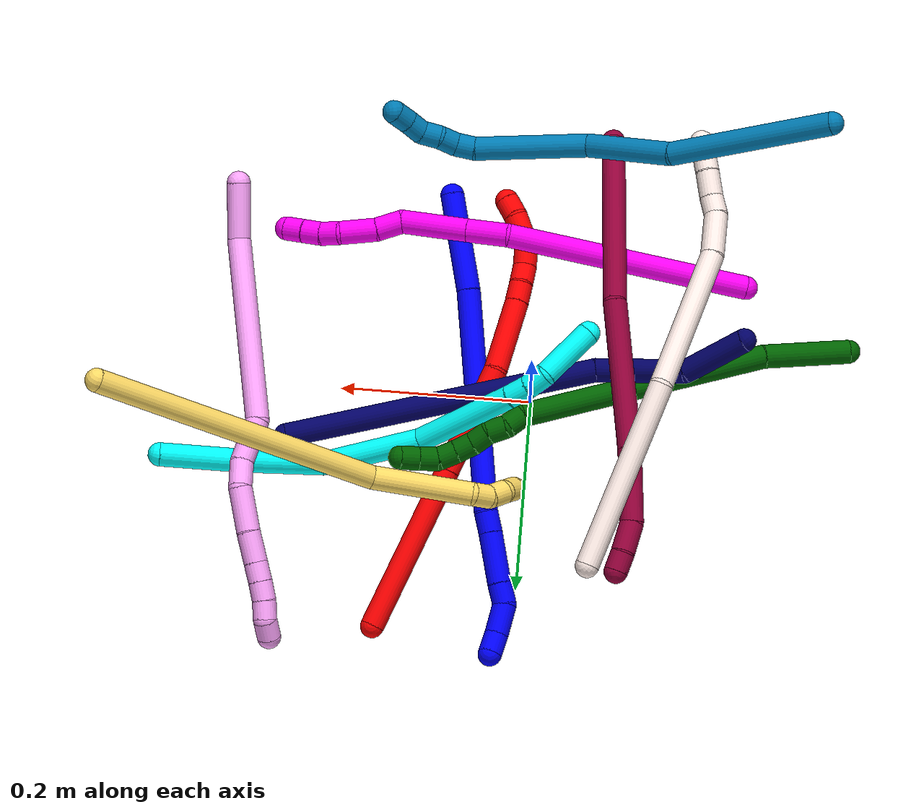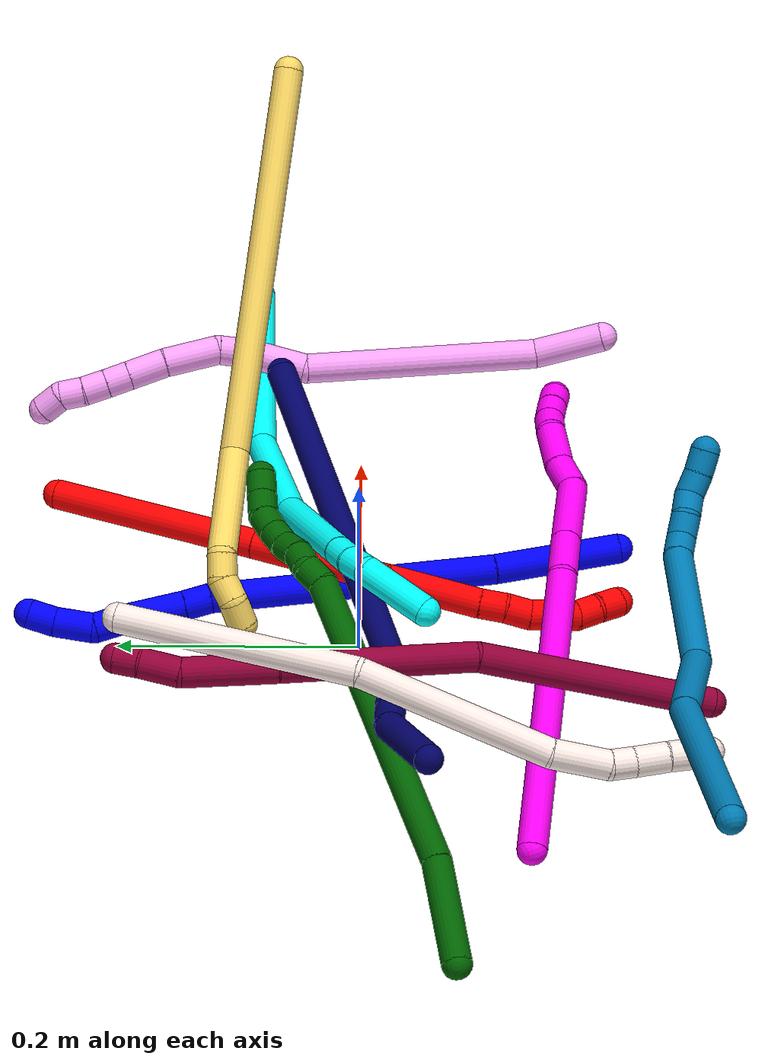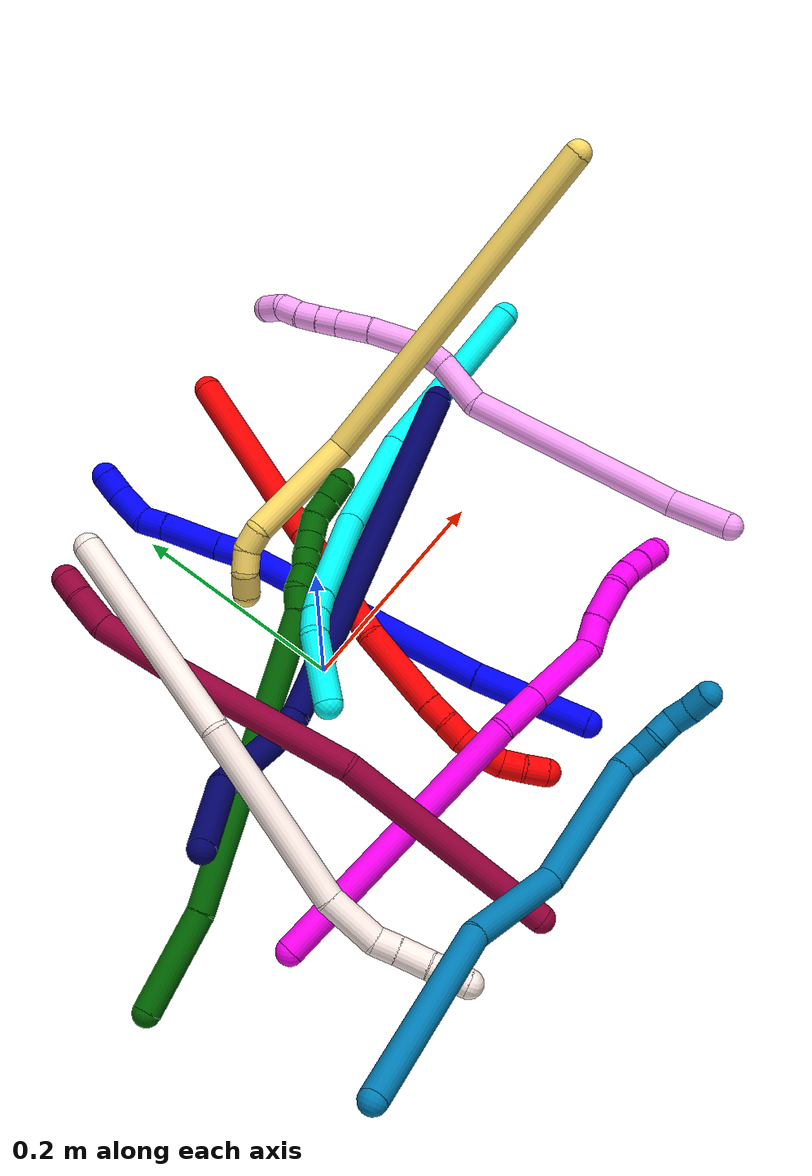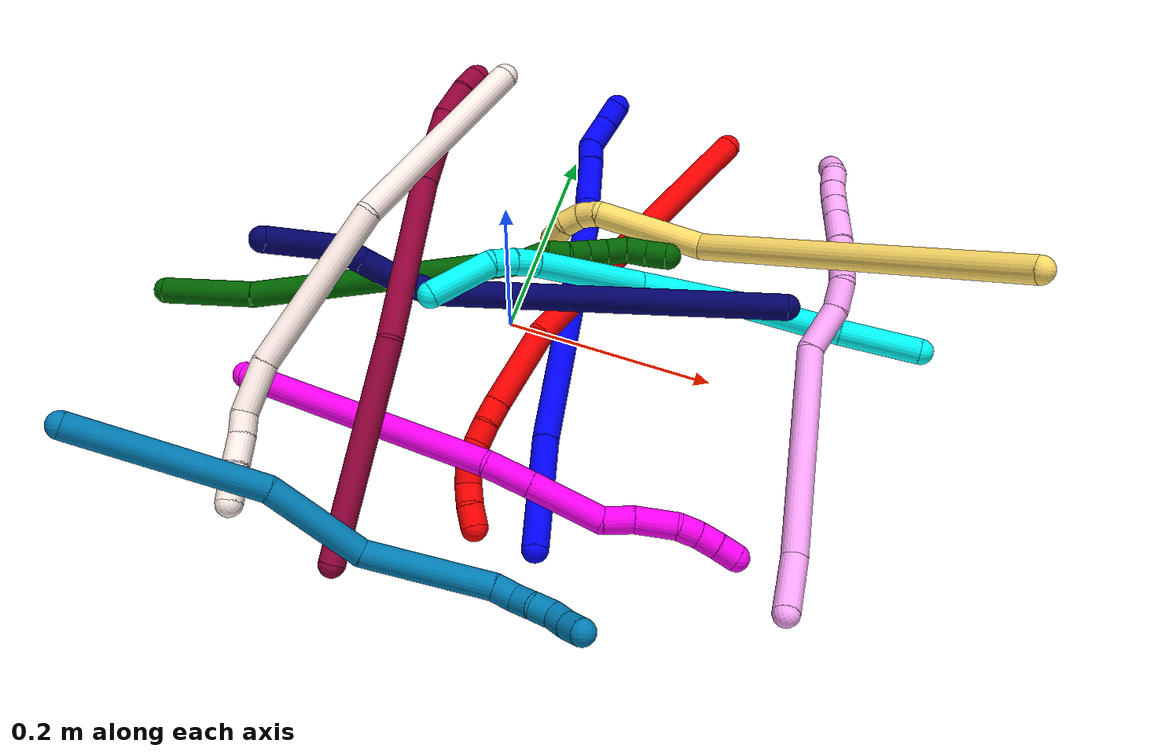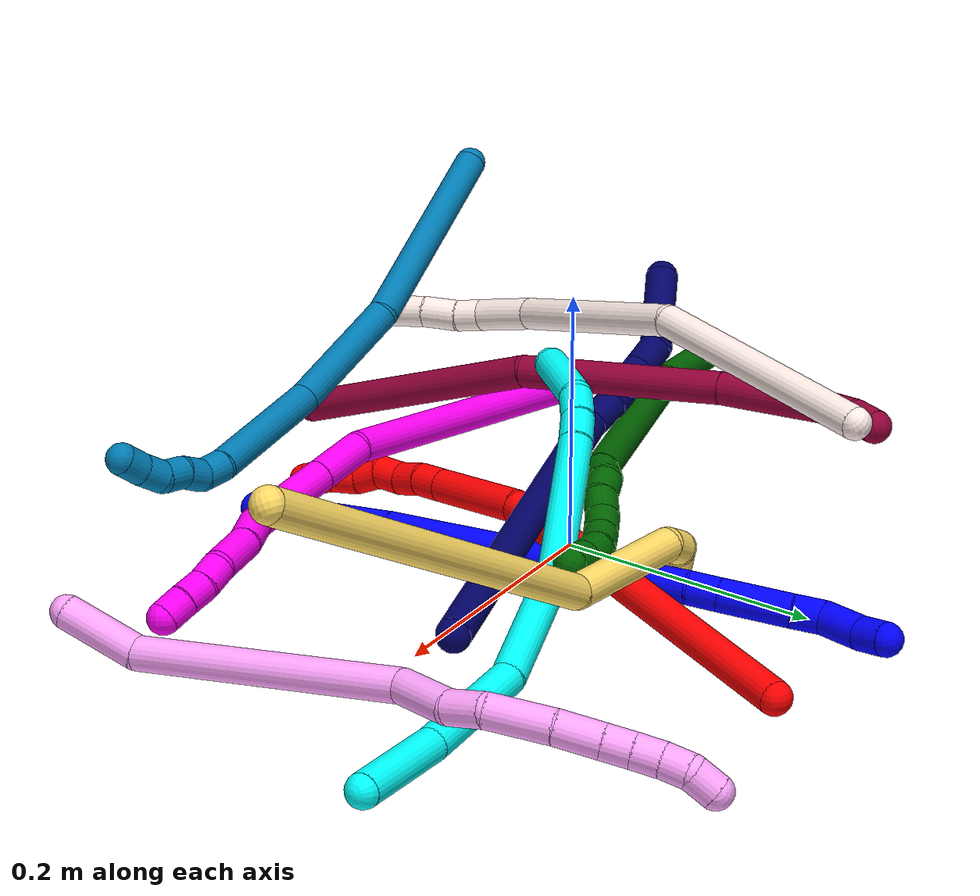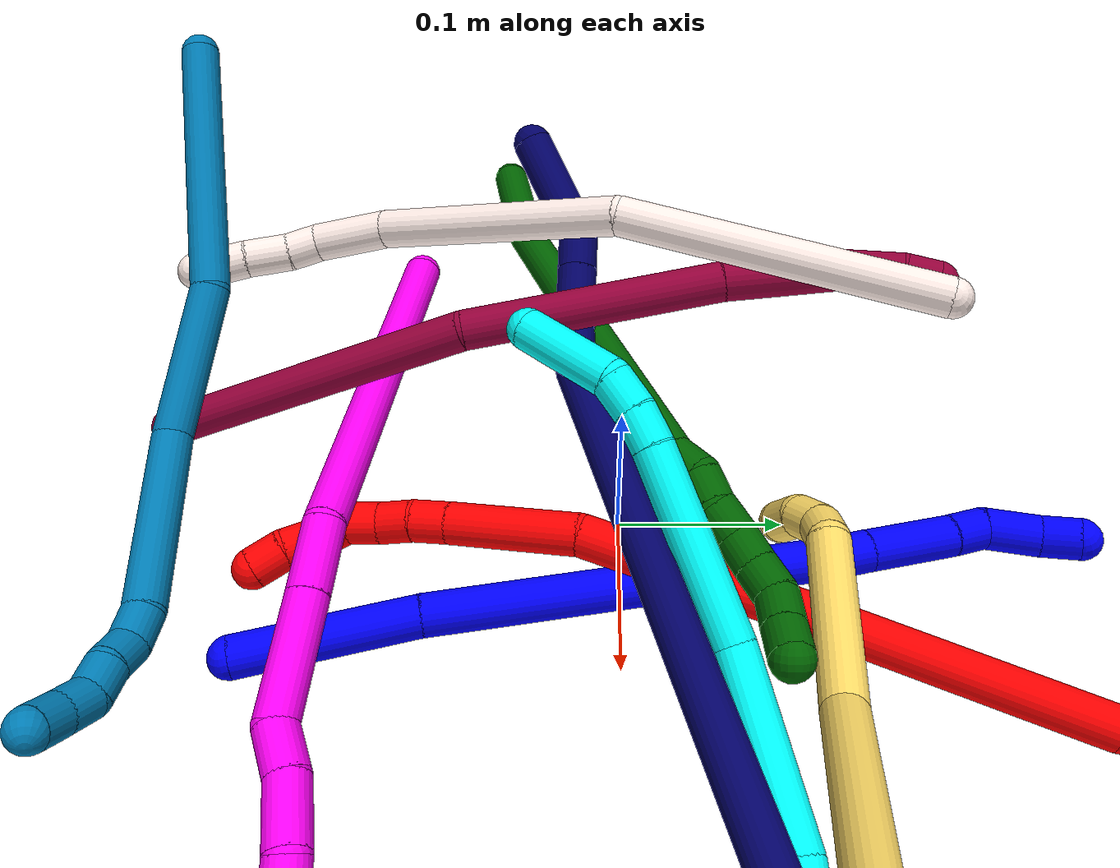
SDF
<sdf version="1.7">
 <world name="default">
  <plugin name="TubeGeneratorPlugin" filename="libtube_generator_plugin.so"/>
  <model name="photoneo_s_sensor">
   <static>1</static>
   <pose>0 0 2 1.57079 1.57079 3.14159</pose>
   <link name="link">
    <inertial><mass>0.1</mass></inertial>
    <sensor name="sensor" type="depth">
     <update_rate>30</update_rate>
     <camera>
      <horizontal_fov>1.22</horizontal_fov>
      <image><width>1920</width><height>1200</height><format>B8G8R8</format></image>
      <clip><near>0.1</near><far>4</far></clip>
      <depth_camera><output>points</output></depth_camera>
     </camera>
     <plugin name="camera_plugin" filename="libgazebo_ros_depth_camera.so">
      <baseline>0.2</baseline>
      <alwaysOn>1</alwaysOn>
      <updateRate>0.0</updateRate>
      <cameraName>camera_ir</cameraName>
      <imageTopicName>/camera/color/image_raw</imageTopicName>
      <cameraInfoTopicName>/camera/color/camera_info</cameraInfoTopicName>
      <depthImageTopicName>/camera/depth/image_raw</depthImageTopicName>
      <depthImageCameraInfoTopicName>/camera/depth/camera_info</depthImageCameraInfoTopicName>
      <pointCloudTopicName>/camera/depth/points</pointCloudTopicName>
      <frameName>fr_optical</frameName>
      <pointCloudCutoff>0.1</pointCloudCutoff>
      <pointCloudCutoffMax>2.0</pointCloudCutoffMax>
      <distortionK1>0</distortionK1>
      <distortionK2>0</distortionK2>
      <distortionK3>0</distortionK3>
      <distortionT1>0</distortionT1>
      <distortionT2>0</distortionT2>
      <CxPrime>0</CxPrime>
      <Cx>0</Cx>
      <Cy>0</Cy>
      <focalLength>0</focalLength>
      <hackBaseline>0</hackBaseline>
     </plugin>
    </sensor>
   </link>
  </model>
  <gravity>0 0 -9.8</gravity>
  <magnetic_field>6e-06 2.3e-05 -4.2e-05</magnetic_field>
  <atmosphere type="adiabatic"/>
  <physics name="default_physics" default="0" type="ode">
   <max_step_size>0.003</max_step_size>
   <real_time_factor>1</real_time_factor>
   <real_time_update_rate>1000</real_time_update_rate>
   <max_contacts>10000</max_contacts>
   <ode>
    <solver>
     <type>quick</type>
     <iters>100</iters>
     <sor>1.3</sor>
     <use_dynamic_moi_rescaling>0</use_dynamic_moi_rescaling>
    </solver>
    <constraints>
     <contact_max_correcting_vel>0</contact_max_correcting_vel>
     <contact_surface_layer>0.001</contact_surface_layer>
     <cfm>0</cfm>
     <erp>0.2</erp>
    </constraints>
   </ode>
  </physics>
  <scene><ambient>0.4 0.4 0.4 1</ambient><background>0.7 0.7 0.7 1</background><shadows>0</shadows></scene>
  <audio><device>default</device></audio>
  <spherical_coordinates>
   <surface_model>EARTH_WGS84</surface_model>
   <latitude_deg>0</latitude_deg>
   <longitude_deg>0</longitude_deg>
   <elevation>0</elevation>
   <heading_deg>0</heading_deg>
  </spherical_coordinates>
  <model name="bin">
   <static>1</static>
   <link name="bottom">
    <collision name="collision-bottom">
     <pose>0 0 -0.01 0 -0 0</pose>
     <geometry><box><size>0.8 0.6 0.02</size></box></geometry>
     <surface>
      <friction><ode><mu>100</mu><mu2>100</mu2></ode></friction>
      <contact><collide_bitmask>65535</collide_bitmask></contact>
     </surface>
    </collision>
   </link>
   <link name="west_wall">
    <collision name="collision-west_wall">
     <pose>-0.41 0 0.1 0 -0 0</pose>
     <geometry><box><size>0.02 0.6 0.2</size></box></geometry>
     <surface>
      <friction><ode><mu>100</mu><mu2>100</mu2></ode></friction>
      <contact><collide_bitmask>65535</collide_bitmask></contact>
     </surface>
    </collision>
   </link>
   <link name="east_wall">
    <collision name="collision-east_wall">
     <pose>0.41 0 0.1 0 -0 0</pose>
     <geometry><box><size>0.02 0.6 0.2</size></box></geometry>
     <surface>
      <friction><ode><mu>100</mu><mu2>100</mu2></ode></friction>
      <contact><collide_bitmask>65535</collide_bitmask></contact>
     </surface>
    </collision>
   </link>
   <link name="south_wall">
    <collision name="collision-south_wall">
     <pose>0 -0.31 0.1 0 -0 0</pose>
     <geometry><box><size>0.8 0.02 0.2</size></box></geometry>
     <surface>
      <friction><ode><mu>100</mu><mu2>100</mu2></ode></friction>
      <contact><collide_bitmask>65535</collide_bitmask></contact>
     </surface>
    </collision>
   </link>
   <link name="north_wall">
    <collision name="collision-north_wall">
     <pose>0 0.31 0.1 0 -0 0</pose>
     <geometry><box><size>0.8 0.02 0.2</size></box></geometry>
     <surface>
      <friction><ode><mu>100</mu><mu2>100</mu2></ode></friction>
      <contact><collide_bitmask>65535</collide_bitmask></contact>
     </surface>
    </collision>
   </link>
  </model>
  <model name="1">
   <static>0</static>
   <link name="1">
    <collision name="collision-cylinder-e_1_1_4">
     <pose>-0.013646 0.050026 -0.011693 -1.80041 -0.259615 0.32622</pose>
     <geometry><cylinder><radius>0.0125</radius><length>0.106312</length></cylinder></geometry>
     <surface>
      <friction><ode><mu>1.16</mu><mu2>1.16</mu2><slip1>0</slip1><slip2>0</slip2></ode></friction>
      <contact><ode><kp>1e+06</kp><kd>1</kd><max_vel>0</max_vel><min_depth>0.001</min_depth></ode></contact>
     </surface>
    </collision>
    <visual name="visual-cylinder-e_1_1_4">
     <pose>-0.013646 0.050026 -0.011693 -1.80041 -0.259615 0.32622</pose>
     <geometry><cylinder><radius>0.0125</radius><length>0.106312</length></cylinder></geometry>
     <material><ambient>0 0 1 1</ambient></material>
    </visual>
    <collision name="collision-cylinder-e_2_4_5">
     <pose>-0.047855 0.214343 -0.050477 -1.80354 -0.173316 0.218873</pose>
     <geometry><cylinder><radius>0.0125</radius><length>0.238487</length></cylinder></geometry>
     <surface>
      <friction><ode><mu>1.16</mu><mu2>1.16</mu2><slip1>0</slip1><slip2>0</slip2></ode></friction>
      <contact><ode><kp>1e+06</kp><kd>1</kd><max_vel>0</max_vel><min_depth>0.001</min_depth></ode></contact>
     </surface>
    </collision>
    <visual name="visual-cylinder-e_2_4_5">
     <pose>-0.047855 0.214343 -0.050477 -1.80354 -0.173316 0.218873</pose>
     <geometry><cylinder><radius>0.0125</radius><length>0.238487</length></cylinder></geometry>
     <material><ambient>0 0 1 1</ambient></material>
    </visual>
    <collision name="collision-cylinder-e_3_5_6">
     <pose>-0.071881 0.338838 -0.08126 -1.918 -0.308883 0.436717</pose>
     <geometry><cylinder><radius>0.0125</radius><length>0.022782</length></cylinder></geometry>
     <surface>
      <friction><ode><mu>1.16</mu><mu2>1.16</mu2><slip1>0</slip1><slip2>0</slip2></ode></friction>
      <contact><ode><kp>1e+06</kp><kd>1</kd><max_vel>0</max_vel><min_depth>0.001</min_depth></ode></contact>
     </surface>
    </collision>
    <visual name="visual-cylinder-e_3_5_6">
     <pose>-0.071881 0.338838 -0.08126 -1.918 -0.308883 0.436717</pose>
     <geometry><cylinder><radius>0.0125</radius><length>0.022782</length></cylinder></geometry>
     <material><ambient>0 0 1 1</ambient></material>
    </visual>
    <collision name="collision-cylinder-e_4_6_7">
     <pose>-0.082468 0.373769 -0.093 -1.88543 -0.267415 0.366308</pose>
     <geometry><cylinder><radius>0.0125</radius><length>0.053924</length></cylinder></geometry>
     <surface>
      <friction><ode><mu>1.16</mu><mu2>1.16</mu2><slip1>0</slip1><slip2>0</slip2></ode></friction>
      <contact><ode><kp>1e+06</kp><kd>1</kd><max_vel>0</max_vel><min_depth>0.001</min_depth></ode></contact>
     </surface>
    </collision>
    <visual name="visual-cylinder-e_4_6_7">
     <pose>-0.082468 0.373769 -0.093 -1.88543 -0.267415 0.366308</pose>
     <geometry><cylinder><radius>0.0125</radius><length>0.053924</length></cylinder></geometry>
     <material><ambient>0 0 1 1</ambient></material>
    </visual>
    <collision name="collision-cylinder-e_5_7_8">
     <pose>-0.093314 0.408548 -0.104611 -1.91154 -0.335732 0.470872</pose>
     <geometry><cylinder><radius>0.0125</radius><length>0.022591</length></cylinder></geometry>
     <surface>
      <friction><ode><mu>1.16</mu><mu2>1.16</mu2><slip1>0</slip1><slip2>0</slip2></ode></friction>
      <contact><ode><kp>1e+06</kp><kd>1</kd><max_vel>0</max_vel><min_depth>0.001</min_depth></ode></contact>
     </surface>
    </collision>
    <visual name="visual-cylinder-e_5_7_8">
     <pose>-0.093314 0.408548 -0.104611 -1.91154 -0.335732 0.470872</pose>
     <geometry><cylinder><radius>0.0125</radius><length>0.022591</length></cylinder></geometry>
     <material><ambient>0 0 1 1</ambient></material>
    </visual>
    <collision name="collision-cylinder-e_6_8_9">
     <pose>-0.094324 0.434439 -0.11201 -1.80833 0.164871 -0.209258</pose>
     <geometry><cylinder><radius>0.0125</radius><length>0.033042</length></cylinder></geometry>
     <surface>
      <friction><ode><mu>1.16</mu><mu2>1.16</mu2><slip1>0</slip1><slip2>0</slip2></ode></friction>
      <contact><ode><kp>1e+06</kp><kd>1</kd><max_vel>0</max_vel><min_depth>0.001</min_depth></ode></contact>
     </surface>
    </collision>
    <visual name="visual-cylinder-e_6_8_9">
     <pose>-0.094324 0.434439 -0.11201 -1.80833 0.164871 -0.209258</pose>
     <geometry><cylinder><radius>0.0125</radius><length>0.033042</length></cylinder></geometry>
     <material><ambient>0 0 1 1</ambient></material>
    </visual>
    <collision name="collision-cylinder-e_7_9_2">
     <pose>-0.089211 0.461436 -0.116489 -1.62849 0.211664 -0.22414</pose>
     <geometry><cylinder><radius>0.0125</radius><length>0.022862</length></cylinder></geometry>
     <surface>
      <friction><ode><mu>1.16</mu><mu2>1.16</mu2><slip1>0</slip1><slip2>0</slip2></ode></friction>
      <contact><ode><kp>1e+06</kp><kd>1</kd><max_vel>0</max_vel><min_depth>0.001</min_depth></ode></contact>
     </surface>
    </collision>
    <visual name="visual-cylinder-e_7_9_2">
     <pose>-0.089211 0.461436 -0.116489 -1.62849 0.211664 -0.22414</pose>
     <geometry><cylinder><radius>0.0125</radius><length>0.022862</length></cylinder></geometry>
     <material><ambient>0 0 1 1</ambient></material>
    </visual>
    <collision name="collision-sphere-2">
     <pose>-0.086809 0.472593 -0.117134 0 -0 0</pose>
     <geometry><sphere><radius>0.0125</radius></sphere></geometry>
     <surface>
      <friction><ode><mu>1.16</mu><mu2>1.16</mu2><slip1>0</slip1><slip2>0</slip2></ode></friction>
      <contact><ode><kp>1e+06</kp><kd>1</kd><max_vel>0</max_vel><min_depth>0.001</min_depth></ode></contact>
     </surface>
    </collision>
    <visual name="visual-sphere-2">
     <pose>-0.086809 0.472593 -0.117134 0 -0 0</pose>
     <geometry><sphere><radius>0.0125</radius></sphere></geometry>
     <material><ambient>0 0 1 1</ambient></material>
    </visual>
    <collision name="collision-sphere-9">
     <pose>-0.091612 0.450278 -0.115845 0 -0 0</pose>
     <geometry><sphere><radius>0.0125</radius></sphere></geometry>
     <surface>
      <friction><ode><mu>1.16</mu><mu2>1.16</mu2><slip1>0</slip1><slip2>0</slip2></ode></friction>
      <contact><ode><kp>1e+06</kp><kd>1</kd><max_vel>0</max_vel><min_depth>0.001</min_depth></ode></contact>
     </surface>
    </collision>
    <visual name="visual-sphere-9">
     <pose>-0.091612 0.450278 -0.115845 0 -0 0</pose>
     <geometry><sphere><radius>0.0125</radius></sphere></geometry>
     <material><ambient>0 0 1 1</ambient></material>
    </visual>
    <collision name="collision-sphere-4">
     <pose>-0.027291 0.100052 -0.023386 0 -0 0</pose>
     <geometry><sphere><radius>0.0125</radius></sphere></geometry>
     <surface>
      <friction><ode><mu>1.16</mu><mu2>1.16</mu2><slip1>0</slip1><slip2>0</slip2></ode></friction>
      <contact><ode><kp>1e+06</kp><kd>1</kd><max_vel>0</max_vel><min_depth>0.001</min_depth></ode></contact>
     </surface>
    </collision>
    <visual name="visual-sphere-4">
     <pose>-0.027291 0.100052 -0.023386 0 -0 0</pose>
     <geometry><sphere><radius>0.0125</radius></sphere></geometry>
     <material><ambient>0 0 1 1</ambient></material>
    </visual>
    <collision name="collision-sphere-1">
     <geometry><sphere><radius>0.0125</radius></sphere></geometry>
     <surface>
      <friction><ode><mu>1.16</mu><mu2>1.16</mu2><slip1>0</slip1><slip2>0</slip2></ode></friction>
      <contact><ode><kp>1e+06</kp><kd>1</kd><max_vel>0</max_vel><min_depth>0.001</min_depth></ode></contact>
     </surface>
    </collision>
    <visual name="visual-sphere-1">
     <geometry><sphere><radius>0.0125</radius></sphere></geometry>
     <material><ambient>0 0 1 1</ambient></material>
    </visual>
    <collision name="collision-sphere-8">
     <pose>-0.097035 0.418599 -0.108175 0 -0 0</pose>
     <geometry><sphere><radius>0.0125</radius></sphere></geometry>
     <surface>
      <friction><ode><mu>1.16</mu><mu2>1.16</mu2><slip1>0</slip1><slip2>0</slip2></ode></friction>
      <contact><ode><kp>1e+06</kp><kd>1</kd><max_vel>0</max_vel><min_depth>0.001</min_depth></ode></contact>
     </surface>
    </collision>
    <visual name="visual-sphere-8">
     <pose>-0.097035 0.418599 -0.108175 0 -0 0</pose>
     <geometry><sphere><radius>0.0125</radius></sphere></geometry>
     <material><ambient>0 0 1 1</ambient></material>
    </visual>
    <collision name="collision-sphere-5">
     <pose>-0.068418 0.328633 -0.077567 0 -0 0</pose>
     <geometry><sphere><radius>0.0125</radius></sphere></geometry>
     <surface>
      <friction><ode><mu>1.16</mu><mu2>1.16</mu2><slip1>0</slip1><slip2>0</slip2></ode></friction>
      <contact><ode><kp>1e+06</kp><kd>1</kd><max_vel>0</max_vel><min_depth>0.001</min_depth></ode></contact>
     </surface>
    </collision>
    <visual name="visual-sphere-5">
     <pose>-0.068418 0.328633 -0.077567 0 -0 0</pose>
     <geometry><sphere><radius>0.0125</radius></sphere></geometry>
     <material><ambient>0 0 1 1</ambient></material>
    </visual>
    <collision name="collision-sphere-6">
     <pose>-0.075344 0.349042 -0.084953 0 -0 0</pose>
     <geometry><sphere><radius>0.0125</radius></sphere></geometry>
     <surface>
      <friction><ode><mu>1.16</mu><mu2>1.16</mu2><slip1>0</slip1><slip2>0</slip2></ode></friction>
      <contact><ode><kp>1e+06</kp><kd>1</kd><max_vel>0</max_vel><min_depth>0.001</min_depth></ode></contact>
     </surface>
    </collision>
    <visual name="visual-sphere-6">
     <pose>-0.075344 0.349042 -0.084953 0 -0 0</pose>
     <geometry><sphere><radius>0.0125</radius></sphere></geometry>
     <material><ambient>0 0 1 1</ambient></material>
    </visual>
    <collision name="collision-sphere-7">
     <pose>-0.089593 0.398496 -0.101047 0 -0 0</pose>
     <geometry><sphere><radius>0.0125</radius></sphere></geometry>
     <surface>
      <friction><ode><mu>1.16</mu><mu2>1.16</mu2><slip1>0</slip1><slip2>0</slip2></ode></friction>
      <contact><ode><kp>1e+06</kp><kd>1</kd><max_vel>0</max_vel><min_depth>0.001</min_depth></ode></contact>
     </surface>
    </collision>
    <visual name="visual-sphere-7">
     <pose>-0.089593 0.398496 -0.101047 0 -0 0</pose>
     <geometry><sphere><radius>0.0125</radius></sphere></geometry>
     <material><ambient>0 0 1 1</ambient></material>
    </visual>
    <inertial>
     <pose>-0.052425 0.236889 -0.05775 0 -0 0</pose>
     <mass>0.5</mass>
     <inertia>
      <ixx>0.001489</ixx>
      <ixy>0</ixy>
      <ixz>0</ixz>
      <iyy>8.5e-05</iyy>
      <iyz>0</iyz>
      <izz>-0.000995</izz>
     </inertia>
    </inertial>
   </link>
   <pose>0.099826 -0.215204 0.011487 0.25276 0.00056 -0.016631</pose>
  </model>
  <model name="2">
   <static>0</static>
   <link name="2">
    <collision name="collision-cylinder-e_1_1_4">
     <pose>-0.027684 -0.085449 0.001557 1.55258 -0.313258 -0.307693</pose>
     <geometry><cylinder><radius>0.0125</radius><length>0.179671</length></cylinder></geometry>
     <surface>
      <friction><ode><mu>1.16</mu><mu2>1.16</mu2><slip1>0</slip1><slip2>0</slip2></ode></friction>
      <contact><ode><kp>1e+06</kp><kd>1</kd><max_vel>0</max_vel><min_depth>0.001</min_depth></ode></contact>
     </surface>
    </collision>
    <visual name="visual-cylinder-e_1_1_4">
     <pose>-0.027684 -0.085449 0.001557 1.55258 -0.313258 -0.307693</pose>
     <geometry><cylinder><radius>0.0125</radius><length>0.179671</length></cylinder></geometry>
     <material><ambient>1 0 0 1</ambient></material>
    </visual>
    <collision name="collision-cylinder-e_2_4_5">
     <pose>-0.073044 -0.227127 0.002657 1.57891 -0.304577 -0.307019</pose>
     <geometry><cylinder><radius>0.0125</radius><length>0.117886</length></cylinder></geometry>
     <surface>
      <friction><ode><mu>1.16</mu><mu2>1.16</mu2><slip1>0</slip1><slip2>0</slip2></ode></friction>
      <contact><ode><kp>1e+06</kp><kd>1</kd><max_vel>0</max_vel><min_depth>0.001</min_depth></ode></contact>
     </surface>
    </collision>
    <visual name="visual-cylinder-e_2_4_5">
     <pose>-0.073044 -0.227127 0.002657 1.57891 -0.304577 -0.307019</pose>
     <geometry><cylinder><radius>0.0125</radius><length>0.117886</length></cylinder></geometry>
     <material><ambient>1 0 0 1</ambient></material>
    </visual>
    <collision name="collision-cylinder-e_3_5_6">
     <pose>-0.096223 -0.321682 -0.005385 1.76619 -0.139933 -0.170209</pose>
     <geometry><cylinder><radius>0.0125</radius><length>0.078912</length></cylinder></geometry>
     <surface>
      <friction><ode><mu>1.16</mu><mu2>1.16</mu2><slip1>0</slip1><slip2>0</slip2></ode></friction>
      <contact><ode><kp>1e+06</kp><kd>1</kd><max_vel>0</max_vel><min_depth>0.001</min_depth></ode></contact>
     </surface>
    </collision>
    <visual name="visual-cylinder-e_3_5_6">
     <pose>-0.096223 -0.321682 -0.005385 1.76619 -0.139933 -0.170209</pose>
     <geometry><cylinder><radius>0.0125</radius><length>0.078912</length></cylinder></geometry>
     <material><ambient>1 0 0 1</ambient></material>
    </visual>
    <collision name="collision-cylinder-e_4_6_7">
     <pose>-0.102573 -0.370609 -0.014505 1.71463 -0.078902 -0.091138</pose>
     <geometry><cylinder><radius>0.0125</radius><length>0.021488</length></cylinder></geometry>
     <surface>
      <friction><ode><mu>1.16</mu><mu2>1.16</mu2><slip1>0</slip1><slip2>0</slip2></ode></friction>
      <contact><ode><kp>1e+06</kp><kd>1</kd><max_vel>0</max_vel><min_depth>0.001</min_depth></ode></contact>
     </surface>
    </collision>
    <visual name="visual-cylinder-e_4_6_7">
     <pose>-0.102573 -0.370609 -0.014505 1.71463 -0.078902 -0.091138</pose>
     <geometry><cylinder><radius>0.0125</radius><length>0.021488</length></cylinder></geometry>
     <material><ambient>1 0 0 1</ambient></material>
    </visual>
    <collision name="collision-cylinder-e_5_7_8">
     <pose>-0.10384 -0.391283 -0.019409 1.89346 -0.039499 -0.054849</pose>
     <geometry><cylinder><radius>0.0125</radius><length>0.021262</length></cylinder></geometry>
     <surface>
      <friction><ode><mu>1.16</mu><mu2>1.16</mu2><slip1>0</slip1><slip2>0</slip2></ode></friction>
      <contact><ode><kp>1e+06</kp><kd>1</kd><max_vel>0</max_vel><min_depth>0.001</min_depth></ode></contact>
     </surface>
    </collision>
    <visual name="visual-cylinder-e_5_7_8">
     <pose>-0.10384 -0.391283 -0.019409 1.89346 -0.039499 -0.054849</pose>
     <geometry><cylinder><radius>0.0125</radius><length>0.021262</length></cylinder></geometry>
     <material><ambient>1 0 0 1</ambient></material>
    </visual>
    <collision name="collision-cylinder-e_6_8_9">
     <pose>-0.103709 -0.411392 -0.023097 1.60258 0.054775 0.056543</pose>
     <geometry><cylinder><radius>0.0125</radius><length>0.02011</length></cylinder></geometry>
     <surface>
      <friction><ode><mu>1.16</mu><mu2>1.16</mu2><slip1>0</slip1><slip2>0</slip2></ode></friction>
      <contact><ode><kp>1e+06</kp><kd>1</kd><max_vel>0</max_vel><min_depth>0.001</min_depth></ode></contact>
     </surface>
    </collision>
    <visual name="visual-cylinder-e_6_8_9">
     <pose>-0.103709 -0.411392 -0.023097 1.60258 0.054775 0.056543</pose>
     <geometry><cylinder><radius>0.0125</radius><length>0.02011</length></cylinder></geometry>
     <material><ambient>1 0 0 1</ambient></material>
    </visual>
    <collision name="collision-cylinder-e_7_9_10">
     <pose>-0.099652 -0.429915 -0.027489 2.01822 0.356545 0.557731</pose>
     <geometry><cylinder><radius>0.0125</radius><length>0.020094</length></cylinder></geometry>
     <surface>
      <friction><ode><mu>1.16</mu><mu2>1.16</mu2><slip1>0</slip1><slip2>0</slip2></ode></friction>
      <contact><ode><kp>1e+06</kp><kd>1</kd><max_vel>0</max_vel><min_depth>0.001</min_depth></ode></contact>
     </surface>
    </collision>
    <visual name="visual-cylinder-e_7_9_10">
     <pose>-0.099652 -0.429915 -0.027489 2.01822 0.356545 0.557731</pose>
     <geometry><cylinder><radius>0.0125</radius><length>0.020094</length></cylinder></geometry>
     <material><ambient>1 0 0 1</ambient></material>
    </visual>
    <collision name="collision-cylinder-e_8_10_11">
     <pose>-0.091427 -0.447371 -0.031609 1.576 0.484382 0.486809</pose>
     <geometry><cylinder><radius>0.0125</radius><length>0.020266</length></cylinder></geometry>
     <surface>
      <friction><ode><mu>1.16</mu><mu2>1.16</mu2><slip1>0</slip1><slip2>0</slip2></ode></friction>
      <contact><ode><kp>1e+06</kp><kd>1</kd><max_vel>0</max_vel><min_depth>0.001</min_depth></ode></contact>
     </surface>
    </collision>
    <visual name="visual-cylinder-e_8_10_11">
     <pose>-0.091427 -0.447371 -0.031609 1.576 0.484382 0.486809</pose>
     <geometry><cylinder><radius>0.0125</radius><length>0.020266</length></cylinder></geometry>
     <material><ambient>1 0 0 1</ambient></material>
    </visual>
    <collision name="collision-cylinder-e_9_11_2">
     <pose>-0.080927 -0.464417 -0.033765 1.82614 0.605618 0.768658</pose>
     <geometry><cylinder><radius>0.0125</radius><length>0.020312</length></cylinder></geometry>
     <surface>
      <friction><ode><mu>1.16</mu><mu2>1.16</mu2><slip1>0</slip1><slip2>0</slip2></ode></friction>
      <contact><ode><kp>1e+06</kp><kd>1</kd><max_vel>0</max_vel><min_depth>0.001</min_depth></ode></contact>
     </surface>
    </collision>
    <visual name="visual-cylinder-e_9_11_2">
     <pose>-0.080927 -0.464417 -0.033765 1.82614 0.605618 0.768658</pose>
     <geometry><cylinder><radius>0.0125</radius><length>0.020312</length></cylinder></geometry>
     <material><ambient>1 0 0 1</ambient></material>
    </visual>
    <collision name="collision-sphere-2">
     <pose>-0.075145 -0.472496 -0.035874 0 -0 0</pose>
     <geometry><sphere><radius>0.0125</radius></sphere></geometry>
     <surface>
      <friction><ode><mu>1.16</mu><mu2>1.16</mu2><slip1>0</slip1><slip2>0</slip2></ode></friction>
      <contact><ode><kp>1e+06</kp><kd>1</kd><max_vel>0</max_vel><min_depth>0.001</min_depth></ode></contact>
     </surface>
    </collision>
    <visual name="visual-sphere-2">
     <pose>-0.075145 -0.472496 -0.035874 0 -0 0</pose>
     <geometry><sphere><radius>0.0125</radius></sphere></geometry>
     <material><ambient>1 0 0 1</ambient></material>
    </visual>
    <collision name="collision-sphere-11">
     <pose>-0.086708 -0.456338 -0.031656 0 -0 0</pose>
     <geometry><sphere><radius>0.0125</radius></sphere></geometry>
     <surface>
      <friction><ode><mu>1.16</mu><mu2>1.16</mu2><slip1>0</slip1><slip2>0</slip2></ode></friction>
      <contact><ode><kp>1e+06</kp><kd>1</kd><max_vel>0</max_vel><min_depth>0.001</min_depth></ode></contact>
     </surface>
    </collision>
    <visual name="visual-sphere-11">
     <pose>-0.086708 -0.456338 -0.031656 0 -0 0</pose>
     <geometry><sphere><radius>0.0125</radius></sphere></geometry>
     <material><ambient>1 0 0 1</ambient></material>
    </visual>
    <collision name="collision-sphere-10">
     <pose>-0.096145 -0.438404 -0.031562 0 -0 0</pose>
     <geometry><sphere><radius>0.0125</radius></sphere></geometry>
     <surface>
      <friction><ode><mu>1.16</mu><mu2>1.16</mu2><slip1>0</slip1><slip2>0</slip2></ode></friction>
      <contact><ode><kp>1e+06</kp><kd>1</kd><max_vel>0</max_vel><min_depth>0.001</min_depth></ode></contact>
     </surface>
    </collision>
    <visual name="visual-sphere-10">
     <pose>-0.096145 -0.438404 -0.031562 0 -0 0</pose>
     <geometry><sphere><radius>0.0125</radius></sphere></geometry>
     <material><ambient>1 0 0 1</ambient></material>
    </visual>
    <collision name="collision-sphere-9">
     <pose>-0.103159 -0.421427 -0.023416 0 -0 0</pose>
     <geometry><sphere><radius>0.0125</radius></sphere></geometry>
     <surface>
      <friction><ode><mu>1.16</mu><mu2>1.16</mu2><slip1>0</slip1><slip2>0</slip2></ode></friction>
      <contact><ode><kp>1e+06</kp><kd>1</kd><max_vel>0</max_vel><min_depth>0.001</min_depth></ode></contact>
     </surface>
    </collision>
    <visual name="visual-sphere-9">
     <pose>-0.103159 -0.421427 -0.023416 0 -0 0</pose>
     <geometry><sphere><radius>0.0125</radius></sphere></geometry>
     <material><ambient>1 0 0 1</ambient></material>
    </visual>
    <collision name="collision-sphere-4">
     <pose>-0.055367 -0.170899 0.003113 0 -0 0</pose>
     <geometry><sphere><radius>0.0125</radius></sphere></geometry>
     <surface>
      <friction><ode><mu>1.16</mu><mu2>1.16</mu2><slip1>0</slip1><slip2>0</slip2></ode></friction>
      <contact><ode><kp>1e+06</kp><kd>1</kd><max_vel>0</max_vel><min_depth>0.001</min_depth></ode></contact>
     </surface>
    </collision>
    <visual name="visual-sphere-4">
     <pose>-0.055367 -0.170899 0.003113 0 -0 0</pose>
     <geometry><sphere><radius>0.0125</radius></sphere></geometry>
     <material><ambient>1 0 0 1</ambient></material>
    </visual>
    <collision name="collision-sphere-1">
     <geometry><sphere><radius>0.0125</radius></sphere></geometry>
     <surface>
      <friction><ode><mu>1.16</mu><mu2>1.16</mu2><slip1>0</slip1><slip2>0</slip2></ode></friction>
      <contact><ode><kp>1e+06</kp><kd>1</kd><max_vel>0</max_vel><min_depth>0.001</min_depth></ode></contact>
     </surface>
    </collision>
    <visual name="visual-sphere-1">
     <geometry><sphere><radius>0.0125</radius></sphere></geometry>
     <material><ambient>1 0 0 1</ambient></material>
    </visual>
    <collision name="collision-sphere-8">
     <pose>-0.10426 -0.401358 -0.022778 0 -0 0</pose>
     <geometry><sphere><radius>0.0125</radius></sphere></geometry>
     <surface>
      <friction><ode><mu>1.16</mu><mu2>1.16</mu2><slip1>0</slip1><slip2>0</slip2></ode></friction>
      <contact><ode><kp>1e+06</kp><kd>1</kd><max_vel>0</max_vel><min_depth>0.001</min_depth></ode></contact>
     </surface>
    </collision>
    <visual name="visual-sphere-8">
     <pose>-0.10426 -0.401358 -0.022778 0 -0 0</pose>
     <geometry><sphere><radius>0.0125</radius></sphere></geometry>
     <material><ambient>1 0 0 1</ambient></material>
    </visual>
    <collision name="collision-sphere-5">
     <pose>-0.09072 -0.283355 0.002201 0 -0 0</pose>
     <geometry><sphere><radius>0.0125</radius></sphere></geometry>
     <surface>
      <friction><ode><mu>1.16</mu><mu2>1.16</mu2><slip1>0</slip1><slip2>0</slip2></ode></friction>
      <contact><ode><kp>1e+06</kp><kd>1</kd><max_vel>0</max_vel><min_depth>0.001</min_depth></ode></contact>
     </surface>
    </collision>
    <visual name="visual-sphere-5">
     <pose>-0.09072 -0.283355 0.002201 0 -0 0</pose>
     <geometry><sphere><radius>0.0125</radius></sphere></geometry>
     <material><ambient>1 0 0 1</ambient></material>
    </visual>
    <collision name="collision-sphere-6">
     <pose>-0.101726 -0.360009 -0.01297 0 -0 0</pose>
     <geometry><sphere><radius>0.0125</radius></sphere></geometry>
     <surface>
      <friction><ode><mu>1.16</mu><mu2>1.16</mu2><slip1>0</slip1><slip2>0</slip2></ode></friction>
      <contact><ode><kp>1e+06</kp><kd>1</kd><max_vel>0</max_vel><min_depth>0.001</min_depth></ode></contact>
     </surface>
    </collision>
    <visual name="visual-sphere-6">
     <pose>-0.101726 -0.360009 -0.01297 0 -0 0</pose>
     <geometry><sphere><radius>0.0125</radius></sphere></geometry>
     <material><ambient>1 0 0 1</ambient></material>
    </visual>
    <collision name="collision-sphere-7">
     <pose>-0.10342 -0.381209 -0.016041 0 -0 0</pose>
     <geometry><sphere><radius>0.0125</radius></sphere></geometry>
     <surface>
      <friction><ode><mu>1.16</mu><mu2>1.16</mu2><slip1>0</slip1><slip2>0</slip2></ode></friction>
      <contact><ode><kp>1e+06</kp><kd>1</kd><max_vel>0</max_vel><min_depth>0.001</min_depth></ode></contact>
     </surface>
    </collision>
    <visual name="visual-sphere-7">
     <pose>-0.10342 -0.381209 -0.016041 0 -0 0</pose>
     <geometry><sphere><radius>0.0125</radius></sphere></geometry>
     <material><ambient>1 0 0 1</ambient></material>
    </visual>
    <inertial>
     <pose>-0.066349 -0.238413 -0.005799 0 -0 0</pose>
     <mass>0.5</mass>
     <inertia>
      <ixx>0.000431</ixx>
      <ixy>0</ixy>
      <ixz>0</ixz>
      <iyy>-0.000166</iyy>
      <iyz>0</iyz>
      <izz>0.000847</izz>
     </inertia>
    </inertial>
   </link>
   <pose>0.145127 0.254556 0.024191 -0.04092 0.050781 -0.058553</pose>
  </model>
  <model name="3">
   <static>0</static>
   <link name="3">
    <collision name="collision-cylinder-e_1_1_4">
     <pose>-0.004501 -0.002953 -0.038275 3.0646 -0.116711 -1.97592</pose>
     <geometry><cylinder><radius>0.0125</radius><length>0.077304</length></cylinder></geometry>
     <surface>
      <friction><ode><mu>1.16</mu><mu2>1.16</mu2><slip1>0</slip1><slip2>0</slip2></ode></friction>
      <contact><ode><kp>1e+06</kp><kd>1</kd><max_vel>0</max_vel><min_depth>0.001</min_depth></ode></contact>
     </surface>
    </collision>
    <visual name="visual-cylinder-e_1_1_4">
     <pose>-0.004501 -0.002953 -0.038275 3.0646 -0.116711 -1.97592</pose>
     <geometry><cylinder><radius>0.0125</radius><length>0.077304</length></cylinder></geometry>
     <material><ambient>0.003922 1 0.996078 1</ambient></material>
    </visual>
    <collision name="collision-cylinder-e_2_4_5">
     <pose>-0.019633 -0.01013 -0.122929 3.05074 -0.224439 -2.37478</pose>
     <geometry><cylinder><radius>0.0125</radius><length>0.095536</length></cylinder></geometry>
     <surface>
      <friction><ode><mu>1.16</mu><mu2>1.16</mu2><slip1>0</slip1><slip2>0</slip2></ode></friction>
      <contact><ode><kp>1e+06</kp><kd>1</kd><max_vel>0</max_vel><min_depth>0.001</min_depth></ode></contact>
     </surface>
    </collision>
    <visual name="visual-cylinder-e_2_4_5">
     <pose>-0.019633 -0.01013 -0.122929 3.05074 -0.224439 -2.37478</pose>
     <geometry><cylinder><radius>0.0125</radius><length>0.095536</length></cylinder></geometry>
     <material><ambient>0.003922 1 0.996078 1</ambient></material>
    </visual>
    <collision name="collision-cylinder-e_3_5_6">
     <pose>-0.054434 -0.029356 -0.214394 2.8204 -0.470557 -1.95306</pose>
     <geometry><cylinder><radius>0.0125</radius><length>0.106621</length></cylinder></geometry>
     <surface>
      <friction><ode><mu>1.16</mu><mu2>1.16</mu2><slip1>0</slip1><slip2>0</slip2></ode></friction>
      <contact><ode><kp>1e+06</kp><kd>1</kd><max_vel>0</max_vel><min_depth>0.001</min_depth></ode></contact>
     </surface>
    </collision>
    <visual name="visual-cylinder-e_3_5_6">
     <pose>-0.054434 -0.029356 -0.214394 2.8204 -0.470557 -1.95306</pose>
     <geometry><cylinder><radius>0.0125</radius><length>0.106621</length></cylinder></geometry>
     <material><ambient>0.003922 1 0.996078 1</ambient></material>
    </visual>
    <collision name="collision-cylinder-e_4_6_7">
     <pose>-0.114604 -0.065471 -0.297287 2.63227 -0.693571 -1.89314</pose>
     <geometry><cylinder><radius>0.0125</radius><length>0.112624</length></cylinder></geometry>
     <surface>
      <friction><ode><mu>1.16</mu><mu2>1.16</mu2><slip1>0</slip1><slip2>0</slip2></ode></friction>
      <contact><ode><kp>1e+06</kp><kd>1</kd><max_vel>0</max_vel><min_depth>0.001</min_depth></ode></contact>
     </surface>
    </collision>
    <visual name="visual-cylinder-e_4_6_7">
     <pose>-0.114604 -0.065471 -0.297287 2.63227 -0.693571 -1.89314</pose>
     <geometry><cylinder><radius>0.0125</radius><length>0.112624</length></cylinder></geometry>
     <material><ambient>0.003922 1 0.996078 1</ambient></material>
    </visual>
    <collision name="collision-cylinder-e_5_7_8">
     <pose>-0.157049 -0.091671 -0.342873 2.56252 -0.606225 -1.61939</pose>
     <geometry><cylinder><radius>0.0125</radius><length>0.022622</length></cylinder></geometry>
     <surface>
      <friction><ode><mu>1.16</mu><mu2>1.16</mu2><slip1>0</slip1><slip2>0</slip2></ode></friction>
      <contact><ode><kp>1e+06</kp><kd>1</kd><max_vel>0</max_vel><min_depth>0.001</min_depth></ode></contact>
     </surface>
    </collision>
    <visual name="visual-cylinder-e_5_7_8">
     <pose>-0.157049 -0.091671 -0.342873 2.56252 -0.606225 -1.61939</pose>
     <geometry><cylinder><radius>0.0125</radius><length>0.022622</length></cylinder></geometry>
     <material><ambient>0.003922 1 0.996078 1</ambient></material>
    </visual>
    <collision name="collision-cylinder-e_6_8_9">
     <pose>-0.169402 -0.103426 -0.357888 2.39697 -0.540864 -1.23465</pose>
     <geometry><cylinder><radius>0.0125</radius><length>0.022954</length></cylinder></geometry>
     <surface>
      <friction><ode><mu>1.16</mu><mu2>1.16</mu2><slip1>0</slip1><slip2>0</slip2></ode></friction>
      <contact><ode><kp>1e+06</kp><kd>1</kd><max_vel>0</max_vel><min_depth>0.001</min_depth></ode></contact>
     </surface>
    </collision>
    <visual name="visual-cylinder-e_6_8_9">
     <pose>-0.169402 -0.103426 -0.357888 2.39697 -0.540864 -1.23465</pose>
     <geometry><cylinder><radius>0.0125</radius><length>0.022954</length></cylinder></geometry>
     <material><ambient>0.003922 1 0.996078 1</ambient></material>
    </visual>
    <collision name="collision-cylinder-e_7_9_2">
     <pose>-0.179527 -0.134911 -0.383502 2.20825 -0.135665 -0.268088</pose>
     <geometry><cylinder><radius>0.0125</radius><length>0.062338</length></cylinder></geometry>
     <surface>
      <friction><ode><mu>1.16</mu><mu2>1.16</mu2><slip1>0</slip1><slip2>0</slip2></ode></friction>
      <contact><ode><kp>1e+06</kp><kd>1</kd><max_vel>0</max_vel><min_depth>0.001</min_depth></ode></contact>
     </surface>
    </collision>
    <visual name="visual-cylinder-e_7_9_2">
     <pose>-0.179527 -0.134911 -0.383502 2.20825 -0.135665 -0.268088</pose>
     <geometry><cylinder><radius>0.0125</radius><length>0.062338</length></cylinder></geometry>
     <material><ambient>0.003922 1 0.996078 1</ambient></material>
    </visual>
    <collision name="collision-sphere-2">
     <pose>-0.183743 -0.159728 -0.401882 0 -0 0</pose>
     <geometry><sphere><radius>0.0125</radius></sphere></geometry>
     <surface>
      <friction><ode><mu>1.16</mu><mu2>1.16</mu2><slip1>0</slip1><slip2>0</slip2></ode></friction>
      <contact><ode><kp>1e+06</kp><kd>1</kd><max_vel>0</max_vel><min_depth>0.001</min_depth></ode></contact>
     </surface>
    </collision>
    <visual name="visual-sphere-2">
     <pose>-0.183743 -0.159728 -0.401882 0 -0 0</pose>
     <geometry><sphere><radius>0.0125</radius></sphere></geometry>
     <material><ambient>0.003922 1 0.996078 1</ambient></material>
    </visual>
    <collision name="collision-sphere-9">
     <pose>-0.175312 -0.110093 -0.365123 0 -0 0</pose>
     <geometry><sphere><radius>0.0125</radius></sphere></geometry>
     <surface>
      <friction><ode><mu>1.16</mu><mu2>1.16</mu2><slip1>0</slip1><slip2>0</slip2></ode></friction>
      <contact><ode><kp>1e+06</kp><kd>1</kd><max_vel>0</max_vel><min_depth>0.001</min_depth></ode></contact>
     </surface>
    </collision>
    <visual name="visual-sphere-9">
     <pose>-0.175312 -0.110093 -0.365123 0 -0 0</pose>
     <geometry><sphere><radius>0.0125</radius></sphere></geometry>
     <material><ambient>0.003922 1 0.996078 1</ambient></material>
    </visual>
    <collision name="collision-sphere-4">
     <pose>-0.009002 -0.005905 -0.076551 0 -0 0</pose>
     <geometry><sphere><radius>0.0125</radius></sphere></geometry>
     <surface>
      <friction><ode><mu>1.16</mu><mu2>1.16</mu2><slip1>0</slip1><slip2>0</slip2></ode></friction>
      <contact><ode><kp>1e+06</kp><kd>1</kd><max_vel>0</max_vel><min_depth>0.001</min_depth></ode></contact>
     </surface>
    </collision>
    <visual name="visual-sphere-4">
     <pose>-0.009002 -0.005905 -0.076551 0 -0 0</pose>
     <geometry><sphere><radius>0.0125</radius></sphere></geometry>
     <material><ambient>0.003922 1 0.996078 1</ambient></material>
    </visual>
    <collision name="collision-sphere-1">
     <geometry><sphere><radius>0.0125</radius></sphere></geometry>
     <surface>
      <friction><ode><mu>1.16</mu><mu2>1.16</mu2><slip1>0</slip1><slip2>0</slip2></ode></friction>
      <contact><ode><kp>1e+06</kp><kd>1</kd><max_vel>0</max_vel><min_depth>0.001</min_depth></ode></contact>
     </surface>
    </collision>
    <visual name="visual-sphere-1">
     <geometry><sphere><radius>0.0125</radius></sphere></geometry>
     <material><ambient>0.003922 1 0.996078 1</ambient></material>
    </visual>
    <collision name="collision-sphere-8">
     <pose>-0.163493 -0.096758 -0.350653 0 -0 0</pose>
     <geometry><sphere><radius>0.0125</radius></sphere></geometry>
     <surface>
      <friction><ode><mu>1.16</mu><mu2>1.16</mu2><slip1>0</slip1><slip2>0</slip2></ode></friction>
      <contact><ode><kp>1e+06</kp><kd>1</kd><max_vel>0</max_vel><min_depth>0.001</min_depth></ode></contact>
     </surface>
    </collision>
    <visual name="visual-sphere-8">
     <pose>-0.163493 -0.096758 -0.350653 0 -0 0</pose>
     <geometry><sphere><radius>0.0125</radius></sphere></geometry>
     <material><ambient>0.003922 1 0.996078 1</ambient></material>
    </visual>
    <collision name="collision-sphere-5">
     <pose>-0.030264 -0.014356 -0.169307 0 -0 0</pose>
     <geometry><sphere><radius>0.0125</radius></sphere></geometry>
     <surface>
      <friction><ode><mu>1.16</mu><mu2>1.16</mu2><slip1>0</slip1><slip2>0</slip2></ode></friction>
      <contact><ode><kp>1e+06</kp><kd>1</kd><max_vel>0</max_vel><min_depth>0.001</min_depth></ode></contact>
     </surface>
    </collision>
    <visual name="visual-sphere-5">
     <pose>-0.030264 -0.014356 -0.169307 0 -0 0</pose>
     <geometry><sphere><radius>0.0125</radius></sphere></geometry>
     <material><ambient>0.003922 1 0.996078 1</ambient></material>
    </visual>
    <collision name="collision-sphere-6">
     <pose>-0.078605 -0.044357 -0.25948 0 -0 0</pose>
     <geometry><sphere><radius>0.0125</radius></sphere></geometry>
     <surface>
      <friction><ode><mu>1.16</mu><mu2>1.16</mu2><slip1>0</slip1><slip2>0</slip2></ode></friction>
      <contact><ode><kp>1e+06</kp><kd>1</kd><max_vel>0</max_vel><min_depth>0.001</min_depth></ode></contact>
     </surface>
    </collision>
    <visual name="visual-sphere-6">
     <pose>-0.078605 -0.044357 -0.25948 0 -0 0</pose>
     <geometry><sphere><radius>0.0125</radius></sphere></geometry>
     <material><ambient>0.003922 1 0.996078 1</ambient></material>
    </visual>
    <collision name="collision-sphere-7">
     <pose>-0.150604 -0.086584 -0.335093 0 -0 0</pose>
     <geometry><sphere><radius>0.0125</radius></sphere></geometry>
     <surface>
      <friction><ode><mu>1.16</mu><mu2>1.16</mu2><slip1>0</slip1><slip2>0</slip2></ode></friction>
      <contact><ode><kp>1e+06</kp><kd>1</kd><max_vel>0</max_vel><min_depth>0.001</min_depth></ode></contact>
     </surface>
    </collision>
    <visual name="visual-sphere-7">
     <pose>-0.150604 -0.086584 -0.335093 0 -0 0</pose>
     <geometry><sphere><radius>0.0125</radius></sphere></geometry>
     <material><ambient>0.003922 1 0.996078 1</ambient></material>
    </visual>
    <inertial>
     <pose>-0.079134 -0.049115 -0.221844 0 -0 0</pose>
     <mass>0.5</mass>
     <inertia>
      <ixx>-0.000403</ixx>
      <ixy>0</ixy>
      <ixz>0</ixz>
      <iyy>-0.000105</iyy>
      <iyz>0</iyz>
      <izz>0.000228</izz>
     </inertia>
    </inertial>
   </link>
   <pose>0.38232 0.089298 0.016773 0.389536 1.37641 0.326675</pose>
  </model>
  <model name="4">
   <static>0</static>
   <link name="4">
    <collision name="collision-cylinder-e_1_1_4">
     <pose>0.009885 0.028311 0.00276 -1.47362 0.334465 -0.303946</pose>
     <geometry><cylinder><radius>0.0125</radius><length>0.060229</length></cylinder></geometry>
     <surface>
      <friction><ode><mu>1.16</mu><mu2>1.16</mu2><slip1>0</slip1><slip2>0</slip2></ode></friction>
      <contact><ode><kp>1e+06</kp><kd>1</kd><max_vel>0</max_vel><min_depth>0.001</min_depth></ode></contact>
     </surface>
    </collision>
    <visual name="visual-cylinder-e_1_1_4">
     <pose>0.009885 0.028311 0.00276 -1.47362 0.334465 -0.303946</pose>
     <geometry><cylinder><radius>0.0125</radius><length>0.060229</length></cylinder></geometry>
     <material><ambient>1 0.65098 0.996078 1</ambient></material>
    </visual>
    <collision name="collision-cylinder-e_2_4_5">
     <pose>0.017518 0.153994 0.032244 -1.30293 -0.022313 0.017015</pose>
     <geometry><cylinder><radius>0.0125</radius><length>0.201994</length></cylinder></geometry>
     <surface>
      <friction><ode><mu>1.16</mu><mu2>1.16</mu2><slip1>0</slip1><slip2>0</slip2></ode></friction>
      <contact><ode><kp>1e+06</kp><kd>1</kd><max_vel>0</max_vel><min_depth>0.001</min_depth></ode></contact>
     </surface>
    </collision>
    <visual name="visual-cylinder-e_2_4_5">
     <pose>0.017518 0.153994 0.032244 -1.30293 -0.022313 0.017015</pose>
     <geometry><cylinder><radius>0.0125</radius><length>0.201994</length></cylinder></geometry>
     <material><ambient>1 0.65098 0.996078 1</ambient></material>
    </visual>
    <collision name="collision-cylinder-e_3_5_6">
     <pose>0.021252 0.270238 0.072485 -0.949321 0.252455 -0.130231</pose>
     <geometry><cylinder><radius>0.0125</radius><length>0.047948</length></cylinder></geometry>
     <surface>
      <friction><ode><mu>1.16</mu><mu2>1.16</mu2><slip1>0</slip1><slip2>0</slip2></ode></friction>
      <contact><ode><kp>1e+06</kp><kd>1</kd><max_vel>0</max_vel><min_depth>0.001</min_depth></ode></contact>
     </surface>
    </collision>
    <visual name="visual-cylinder-e_3_5_6">
     <pose>0.021252 0.270238 0.072485 -0.949321 0.252455 -0.130231</pose>
     <geometry><cylinder><radius>0.0125</radius><length>0.047948</length></cylinder></geometry>
     <material><ambient>1 0.65098 0.996078 1</ambient></material>
    </visual>
    <collision name="collision-cylinder-e_4_6_7">
     <pose>0.026803 0.30225 0.09248 -1.11261 -0.029879 0.01858</pose>
     <geometry><cylinder><radius>0.0125</radius><length>0.02931</length></cylinder></geometry>
     <surface>
      <friction><ode><mu>1.16</mu><mu2>1.16</mu2><slip1>0</slip1><slip2>0</slip2></ode></friction>
      <contact><ode><kp>1e+06</kp><kd>1</kd><max_vel>0</max_vel><min_depth>0.001</min_depth></ode></contact>
     </surface>
    </collision>
    <visual name="visual-cylinder-e_4_6_7">
     <pose>0.026803 0.30225 0.09248 -1.11261 -0.029879 0.01858</pose>
     <geometry><cylinder><radius>0.0125</radius><length>0.02931</length></cylinder></geometry>
     <material><ambient>1 0.65098 0.996078 1</ambient></material>
    </visual>
    <collision name="collision-cylinder-e_5_7_8">
     <pose>0.027801 0.338859 0.101274 -1.47251 0.06078 -0.055084</pose>
     <geometry><cylinder><radius>0.0125</radius><length>0.047259</length></cylinder></geometry>
     <surface>
      <friction><ode><mu>1.16</mu><mu2>1.16</mu2><slip1>0</slip1><slip2>0</slip2></ode></friction>
      <contact><ode><kp>1e+06</kp><kd>1</kd><max_vel>0</max_vel><min_depth>0.001</min_depth></ode></contact>
     </surface>
    </collision>
    <visual name="visual-cylinder-e_5_7_8">
     <pose>0.027801 0.338859 0.101274 -1.47251 0.06078 -0.055084</pose>
     <geometry><cylinder><radius>0.0125</radius><length>0.047259</length></cylinder></geometry>
     <material><ambient>1 0.65098 0.996078 1</ambient></material>
    </visual>
    <collision name="collision-cylinder-e_6_8_9">
     <pose>0.030901 0.378523 0.10347 -1.57809 0.102482 -0.103231</pose>
     <geometry><cylinder><radius>0.0125</radius><length>0.032556</length></cylinder></geometry>
     <surface>
      <friction><ode><mu>1.16</mu><mu2>1.16</mu2><slip1>0</slip1><slip2>0</slip2></ode></friction>
      <contact><ode><kp>1e+06</kp><kd>1</kd><max_vel>0</max_vel><min_depth>0.001</min_depth></ode></contact>
     </surface>
    </collision>
    <visual name="visual-cylinder-e_6_8_9">
     <pose>0.030901 0.378523 0.10347 -1.57809 0.102482 -0.103231</pose>
     <geometry><cylinder><radius>0.0125</radius><length>0.032556</length></cylinder></geometry>
     <material><ambient>1 0.65098 0.996078 1</ambient></material>
    </visual>
    <collision name="collision-cylinder-e_7_9_10">
     <pose>0.033617 0.404835 0.103291 -1.57687 0.103473 -0.104102</pose>
     <geometry><cylinder><radius>0.0125</radius><length>0.020349</length></cylinder></geometry>
     <surface>
      <friction><ode><mu>1.16</mu><mu2>1.16</mu2><slip1>0</slip1><slip2>0</slip2></ode></friction>
      <contact><ode><kp>1e+06</kp><kd>1</kd><max_vel>0</max_vel><min_depth>0.001</min_depth></ode></contact>
     </surface>
    </collision>
    <visual name="visual-cylinder-e_7_9_10">
     <pose>0.033617 0.404835 0.103291 -1.57687 0.103473 -0.104102</pose>
     <geometry><cylinder><radius>0.0125</radius><length>0.020349</length></cylinder></geometry>
     <material><ambient>1 0.65098 0.996078 1</ambient></material>
    </visual>
    <collision name="collision-cylinder-e_8_10_11">
     <pose>0.035919 0.425013 0.103377 -1.55611 0.123735 -0.121935</pose>
     <geometry><cylinder><radius>0.0125</radius><length>0.020273</length></cylinder></geometry>
     <surface>
      <friction><ode><mu>1.16</mu><mu2>1.16</mu2><slip1>0</slip1><slip2>0</slip2></ode></friction>
      <contact><ode><kp>1e+06</kp><kd>1</kd><max_vel>0</max_vel><min_depth>0.001</min_depth></ode></contact>
     </surface>
    </collision>
    <visual name="visual-cylinder-e_8_10_11">
     <pose>0.035919 0.425013 0.103377 -1.55611 0.123735 -0.121935</pose>
     <geometry><cylinder><radius>0.0125</radius><length>0.020273</length></cylinder></geometry>
     <material><ambient>1 0.65098 0.996078 1</ambient></material>
    </visual>
    <collision name="collision-cylinder-e_9_11_12">
     <pose>0.039372 0.444739 0.104889 -1.43056 0.221779 -0.192865</pose>
     <geometry><cylinder><radius>0.0125</radius><length>0.020017</length></cylinder></geometry>
     <surface>
      <friction><ode><mu>1.16</mu><mu2>1.16</mu2><slip1>0</slip1><slip2>0</slip2></ode></friction>
      <contact><ode><kp>1e+06</kp><kd>1</kd><max_vel>0</max_vel><min_depth>0.001</min_depth></ode></contact>
     </surface>
    </collision>
    <visual name="visual-cylinder-e_9_11_12">
     <pose>0.039372 0.444739 0.104889 -1.43056 0.221779 -0.192865</pose>
     <geometry><cylinder><radius>0.0125</radius><length>0.020017</length></cylinder></geometry>
     <material><ambient>1 0.65098 0.996078 1</ambient></material>
    </visual>
    <collision name="collision-cylinder-e_10_12_2">
     <pose>0.045944 0.462947 0.10332 -1.90173 0.450717 -0.62153</pose>
     <geometry><cylinder><radius>0.0125</radius><length>0.020065</length></cylinder></geometry>
     <surface>
      <friction><ode><mu>1.16</mu><mu2>1.16</mu2><slip1>0</slip1><slip2>0</slip2></ode></friction>
      <contact><ode><kp>1e+06</kp><kd>1</kd><max_vel>0</max_vel><min_depth>0.001</min_depth></ode></contact>
     </surface>
    </collision>
    <visual name="visual-cylinder-e_10_12_2">
     <pose>0.045944 0.462947 0.10332 -1.90173 0.450717 -0.62153</pose>
     <geometry><cylinder><radius>0.0125</radius><length>0.020065</length></cylinder></geometry>
     <material><ambient>1 0.65098 0.996078 1</ambient></material>
    </visual>
    <collision name="collision-sphere-2">
     <pose>0.050314 0.471487 0.100385 0 -0 0</pose>
     <geometry><sphere><radius>0.0125</radius></sphere></geometry>
     <surface>
      <friction><ode><mu>1.16</mu><mu2>1.16</mu2><slip1>0</slip1><slip2>0</slip2></ode></friction>
      <contact><ode><kp>1e+06</kp><kd>1</kd><max_vel>0</max_vel><min_depth>0.001</min_depth></ode></contact>
     </surface>
    </collision>
    <visual name="visual-sphere-2">
     <pose>0.050314 0.471487 0.100385 0 -0 0</pose>
     <geometry><sphere><radius>0.0125</radius></sphere></geometry>
     <material><ambient>1 0.65098 0.996078 1</ambient></material>
    </visual>
    <collision name="collision-sphere-12">
     <pose>0.041573 0.454406 0.106254 0 -0 0</pose>
     <geometry><sphere><radius>0.0125</radius></sphere></geometry>
     <surface>
      <friction><ode><mu>1.16</mu><mu2>1.16</mu2><slip1>0</slip1><slip2>0</slip2></ode></friction>
      <contact><ode><kp>1e+06</kp><kd>1</kd><max_vel>0</max_vel><min_depth>0.001</min_depth></ode></contact>
     </surface>
    </collision>
    <visual name="visual-sphere-12">
     <pose>0.041573 0.454406 0.106254 0 -0 0</pose>
     <geometry><sphere><radius>0.0125</radius></sphere></geometry>
     <material><ambient>1 0.65098 0.996078 1</ambient></material>
    </visual>
    <collision name="collision-sphere-11">
     <pose>0.03717 0.435071 0.103525 0 -0 0</pose>
     <geometry><sphere><radius>0.0125</radius></sphere></geometry>
     <surface>
      <friction><ode><mu>1.16</mu><mu2>1.16</mu2><slip1>0</slip1><slip2>0</slip2></ode></friction>
      <contact><ode><kp>1e+06</kp><kd>1</kd><max_vel>0</max_vel><min_depth>0.001</min_depth></ode></contact>
     </surface>
    </collision>
    <visual name="visual-sphere-11">
     <pose>0.03717 0.435071 0.103525 0 -0 0</pose>
     <geometry><sphere><radius>0.0125</radius></sphere></geometry>
     <material><ambient>1 0.65098 0.996078 1</ambient></material>
    </visual>
    <collision name="collision-sphere-10">
     <pose>0.034668 0.414955 0.103229 0 -0 0</pose>
     <geometry><sphere><radius>0.0125</radius></sphere></geometry>
     <surface>
      <friction><ode><mu>1.16</mu><mu2>1.16</mu2><slip1>0</slip1><slip2>0</slip2></ode></friction>
      <contact><ode><kp>1e+06</kp><kd>1</kd><max_vel>0</max_vel><min_depth>0.001</min_depth></ode></contact>
     </surface>
    </collision>
    <visual name="visual-sphere-10">
     <pose>0.034668 0.414955 0.103229 0 -0 0</pose>
     <geometry><sphere><radius>0.0125</radius></sphere></geometry>
     <material><ambient>1 0.65098 0.996078 1</ambient></material>
    </visual>
    <collision name="collision-sphere-9">
     <pose>0.032566 0.394716 0.103352 0 -0 0</pose>
     <geometry><sphere><radius>0.0125</radius></sphere></geometry>
     <surface>
      <friction><ode><mu>1.16</mu><mu2>1.16</mu2><slip1>0</slip1><slip2>0</slip2></ode></friction>
      <contact><ode><kp>1e+06</kp><kd>1</kd><max_vel>0</max_vel><min_depth>0.001</min_depth></ode></contact>
     </surface>
    </collision>
    <visual name="visual-sphere-9">
     <pose>0.032566 0.394716 0.103352 0 -0 0</pose>
     <geometry><sphere><radius>0.0125</radius></sphere></geometry>
     <material><ambient>1 0.65098 0.996078 1</ambient></material>
    </visual>
    <collision name="collision-sphere-4">
     <pose>0.019771 0.056623 0.00552 0 -0 0</pose>
     <geometry><sphere><radius>0.0125</radius></sphere></geometry>
     <surface>
      <friction><ode><mu>1.16</mu><mu2>1.16</mu2><slip1>0</slip1><slip2>0</slip2></ode></friction>
      <contact><ode><kp>1e+06</kp><kd>1</kd><max_vel>0</max_vel><min_depth>0.001</min_depth></ode></contact>
     </surface>
    </collision>
    <visual name="visual-sphere-4">
     <pose>0.019771 0.056623 0.00552 0 -0 0</pose>
     <geometry><sphere><radius>0.0125</radius></sphere></geometry>
     <material><ambient>1 0.65098 0.996078 1</ambient></material>
    </visual>
    <collision name="collision-sphere-1">
     <geometry><sphere><radius>0.0125</radius></sphere></geometry>
     <surface>
      <friction><ode><mu>1.16</mu><mu2>1.16</mu2><slip1>0</slip1><slip2>0</slip2></ode></friction>
      <contact><ode><kp>1e+06</kp><kd>1</kd><max_vel>0</max_vel><min_depth>0.001</min_depth></ode></contact>
     </surface>
    </collision>
    <visual name="visual-sphere-1">
     <geometry><sphere><radius>0.0125</radius></sphere></geometry>
     <material><ambient>1 0.65098 0.996078 1</ambient></material>
    </visual>
    <collision name="collision-sphere-8">
     <pose>0.029236 0.362331 0.103589 0 -0 0</pose>
     <geometry><sphere><radius>0.0125</radius></sphere></geometry>
     <surface>
      <friction><ode><mu>1.16</mu><mu2>1.16</mu2><slip1>0</slip1><slip2>0</slip2></ode></friction>
      <contact><ode><kp>1e+06</kp><kd>1</kd><max_vel>0</max_vel><min_depth>0.001</min_depth></ode></contact>
     </surface>
    </collision>
    <visual name="visual-sphere-8">
     <pose>0.029236 0.362331 0.103589 0 -0 0</pose>
     <geometry><sphere><radius>0.0125</radius></sphere></geometry>
     <material><ambient>1 0.65098 0.996078 1</ambient></material>
    </visual>
    <collision name="collision-sphere-5">
     <pose>0.015264 0.251365 0.058969 0 -0 0</pose>
     <geometry><sphere><radius>0.0125</radius></sphere></geometry>
     <surface>
      <friction><ode><mu>1.16</mu><mu2>1.16</mu2><slip1>0</slip1><slip2>0</slip2></ode></friction>
      <contact><ode><kp>1e+06</kp><kd>1</kd><max_vel>0</max_vel><min_depth>0.001</min_depth></ode></contact>
     </surface>
    </collision>
    <visual name="visual-sphere-5">
     <pose>0.015264 0.251365 0.058969 0 -0 0</pose>
     <geometry><sphere><radius>0.0125</radius></sphere></geometry>
     <material><ambient>1 0.65098 0.996078 1</ambient></material>
    </visual>
    <collision name="collision-sphere-6">
     <pose>0.027241 0.289112 0.086001 0 -0 0</pose>
     <geometry><sphere><radius>0.0125</radius></sphere></geometry>
     <surface>
      <friction><ode><mu>1.16</mu><mu2>1.16</mu2><slip1>0</slip1><slip2>0</slip2></ode></friction>
      <contact><ode><kp>1e+06</kp><kd>1</kd><max_vel>0</max_vel><min_depth>0.001</min_depth></ode></contact>
     </surface>
    </collision>
    <visual name="visual-sphere-6">
     <pose>0.027241 0.289112 0.086001 0 -0 0</pose>
     <geometry><sphere><radius>0.0125</radius></sphere></geometry>
     <material><ambient>1 0.65098 0.996078 1</ambient></material>
    </visual>
    <collision name="collision-sphere-7">
     <pose>0.026365 0.315387 0.09896 0 -0 0</pose>
     <geometry><sphere><radius>0.0125</radius></sphere></geometry>
     <surface>
      <friction><ode><mu>1.16</mu><mu2>1.16</mu2><slip1>0</slip1><slip2>0</slip2></ode></friction>
      <contact><ode><kp>1e+06</kp><kd>1</kd><max_vel>0</max_vel><min_depth>0.001</min_depth></ode></contact>
     </surface>
    </collision>
    <visual name="visual-sphere-7">
     <pose>0.026365 0.315387 0.09896 0 -0 0</pose>
     <geometry><sphere><radius>0.0125</radius></sphere></geometry>
     <material><ambient>1 0.65098 0.996078 1</ambient></material>
    </visual>
    <inertial>
     <pose>0.022761 0.236021 0.058781 0 -0 0</pose>
     <mass>0.5</mass>
     <inertia>
      <ixx>0.000753</ixx>
      <ixy>0</ixy>
      <ixz>0</ixz>
      <iyy>0.000237</iyy>
      <iyz>0</iyz>
      <izz>-0.000709</izz>
     </inertia>
    </inertial>
   </link>
   <pose>0.325208 -0.206362 0.028454 -0.137081 0.87442 0.275096</pose>
  </model>
  <model name="5">
   <static>0</static>
   <link name="5">
    <collision name="collision-cylinder-e_1_1_4">
     <pose>-0.154737 0.043815 0.039171 -0.841291 -1.20781 0.598688</pose>
     <geometry><cylinder><radius>0.0125</radius><length>0.331045</length></cylinder></geometry>
     <surface>
      <friction><ode><mu>1.16</mu><mu2>1.16</mu2><slip1>0</slip1><slip2>0</slip2></ode></friction>
      <contact><ode><kp>1e+06</kp><kd>1</kd><max_vel>0</max_vel><min_depth>0.001</min_depth></ode></contact>
     </surface>
    </collision>
    <visual name="visual-cylinder-e_1_1_4">
     <pose>-0.154737 0.043815 0.039171 -0.841291 -1.20781 0.598688</pose>
     <geometry><cylinder><radius>0.0125</radius><length>0.331045</length></cylinder></geometry>
     <material><ambient>1 0.858824 0.4 1</ambient></material>
    </visual>
    <collision name="collision-cylinder-e_2_4_5">
     <pose>-0.361501 0.089434 0.068497 -2.96036 -1.38072 2.92244</pose>
     <geometry><cylinder><radius>0.0125</radius><length>0.105962</length></cylinder></geometry>
     <surface>
      <friction><ode><mu>1.16</mu><mu2>1.16</mu2><slip1>0</slip1><slip2>0</slip2></ode></friction>
      <contact><ode><kp>1e+06</kp><kd>1</kd><max_vel>0</max_vel><min_depth>0.001</min_depth></ode></contact>
     </surface>
    </collision>
    <visual name="visual-cylinder-e_2_4_5">
     <pose>-0.361501 0.089434 0.068497 -2.96036 -1.38072 2.92244</pose>
     <geometry><cylinder><radius>0.0125</radius><length>0.105962</length></cylinder></geometry>
     <material><ambient>1 0.858824 0.4 1</ambient></material>
    </visual>
    <collision name="collision-cylinder-e_3_5_6">
     <pose>-0.422997 0.095123 0.059986 -1.23981 -1.16147 0.876079</pose>
     <geometry><cylinder><radius>0.0125</radius><length>0.020644</length></cylinder></geometry>
     <surface>
      <friction><ode><mu>1.16</mu><mu2>1.16</mu2><slip1>0</slip1><slip2>0</slip2></ode></friction>
      <contact><ode><kp>1e+06</kp><kd>1</kd><max_vel>0</max_vel><min_depth>0.001</min_depth></ode></contact>
     </surface>
    </collision>
    <visual name="visual-cylinder-e_3_5_6">
     <pose>-0.422997 0.095123 0.059986 -1.23981 -1.16147 0.876079</pose>
     <geometry><cylinder><radius>0.0125</radius><length>0.020644</length></cylinder></geometry>
     <material><ambient>1 0.858824 0.4 1</ambient></material>
    </visual>
    <collision name="collision-cylinder-e_4_6_7">
     <pose>-0.439439 0.106183 0.060792 -1.64443 -0.769736 0.822381</pose>
     <geometry><cylinder><radius>0.0125</radius><length>0.020038</length></cylinder></geometry>
     <surface>
      <friction><ode><mu>1.16</mu><mu2>1.16</mu2><slip1>0</slip1><slip2>0</slip2></ode></friction>
      <contact><ode><kp>1e+06</kp><kd>1</kd><max_vel>0</max_vel><min_depth>0.001</min_depth></ode></contact>
     </surface>
    </collision>
    <visual name="visual-cylinder-e_4_6_7">
     <pose>-0.439439 0.106183 0.060792 -1.64443 -0.769736 0.822381</pose>
     <geometry><cylinder><radius>0.0125</radius><length>0.020038</length></cylinder></geometry>
     <material><ambient>1 0.858824 0.4 1</ambient></material>
    </visual>
    <collision name="collision-cylinder-e_5_7_2">
     <pose>-0.451883 0.122368 0.063915 -1.18564 -0.512632 0.3495</pose>
     <geometry><cylinder><radius>0.0125</radius><length>0.022311</length></cylinder></geometry>
     <surface>
      <friction><ode><mu>1.16</mu><mu2>1.16</mu2><slip1>0</slip1><slip2>0</slip2></ode></friction>
      <contact><ode><kp>1e+06</kp><kd>1</kd><max_vel>0</max_vel><min_depth>0.001</min_depth></ode></contact>
     </surface>
    </collision>
    <visual name="visual-cylinder-e_5_7_2">
     <pose>-0.451883 0.122368 0.063915 -1.18564 -0.512632 0.3495</pose>
     <geometry><cylinder><radius>0.0125</radius><length>0.022311</length></cylinder></geometry>
     <material><ambient>1 0.858824 0.4 1</ambient></material>
    </visual>
    <collision name="collision-sphere-2">
     <pose>-0.457355 0.131377 0.067567 0 -0 0</pose>
     <geometry><sphere><radius>0.0125</radius></sphere></geometry>
     <surface>
      <friction><ode><mu>1.16</mu><mu2>1.16</mu2><slip1>0</slip1><slip2>0</slip2></ode></friction>
      <contact><ode><kp>1e+06</kp><kd>1</kd><max_vel>0</max_vel><min_depth>0.001</min_depth></ode></contact>
     </surface>
    </collision>
    <visual name="visual-sphere-2">
     <pose>-0.457355 0.131377 0.067567 0 -0 0</pose>
     <geometry><sphere><radius>0.0125</radius></sphere></geometry>
     <material><ambient>1 0.858824 0.4 1</ambient></material>
    </visual>
    <collision name="collision-sphere-7">
     <pose>-0.446412 0.113358 0.060262 0 -0 0</pose>
     <geometry><sphere><radius>0.0125</radius></sphere></geometry>
     <surface>
      <friction><ode><mu>1.16</mu><mu2>1.16</mu2><slip1>0</slip1><slip2>0</slip2></ode></friction>
      <contact><ode><kp>1e+06</kp><kd>1</kd><max_vel>0</max_vel><min_depth>0.001</min_depth></ode></contact>
     </surface>
    </collision>
    <visual name="visual-sphere-7">
     <pose>-0.446412 0.113358 0.060262 0 -0 0</pose>
     <geometry><sphere><radius>0.0125</radius></sphere></geometry>
     <material><ambient>1 0.858824 0.4 1</ambient></material>
    </visual>
    <collision name="collision-sphere-6">
     <pose>-0.432466 0.099008 0.061321 0 -0 0</pose>
     <geometry><sphere><radius>0.0125</radius></sphere></geometry>
     <surface>
      <friction><ode><mu>1.16</mu><mu2>1.16</mu2><slip1>0</slip1><slip2>0</slip2></ode></friction>
      <contact><ode><kp>1e+06</kp><kd>1</kd><max_vel>0</max_vel><min_depth>0.001</min_depth></ode></contact>
     </surface>
    </collision>
    <visual name="visual-sphere-6">
     <pose>-0.432466 0.099008 0.061321 0 -0 0</pose>
     <geometry><sphere><radius>0.0125</radius></sphere></geometry>
     <material><ambient>1 0.858824 0.4 1</ambient></material>
    </visual>
    <collision name="collision-sphere-5">
     <pose>-0.413528 0.091238 0.058651 0 -0 0</pose>
     <geometry><sphere><radius>0.0125</radius></sphere></geometry>
     <surface>
      <friction><ode><mu>1.16</mu><mu2>1.16</mu2><slip1>0</slip1><slip2>0</slip2></ode></friction>
      <contact><ode><kp>1e+06</kp><kd>1</kd><max_vel>0</max_vel><min_depth>0.001</min_depth></ode></contact>
     </surface>
    </collision>
    <visual name="visual-sphere-5">
     <pose>-0.413528 0.091238 0.058651 0 -0 0</pose>
     <geometry><sphere><radius>0.0125</radius></sphere></geometry>
     <material><ambient>1 0.858824 0.4 1</ambient></material>
    </visual>
    <collision name="collision-sphere-1">
     <geometry><sphere><radius>0.0125</radius></sphere></geometry>
     <surface>
      <friction><ode><mu>1.16</mu><mu2>1.16</mu2><slip1>0</slip1><slip2>0</slip2></ode></friction>
      <contact><ode><kp>1e+06</kp><kd>1</kd><max_vel>0</max_vel><min_depth>0.001</min_depth></ode></contact>
     </surface>
    </collision>
    <visual name="visual-sphere-1">
     <geometry><sphere><radius>0.0125</radius></sphere></geometry>
     <material><ambient>1 0.858824 0.4 1</ambient></material>
    </visual>
    <collision name="collision-sphere-4">
     <pose>-0.309474 0.087629 0.078343 0 -0 0</pose>
     <geometry><sphere><radius>0.0125</radius></sphere></geometry>
     <surface>
      <friction><ode><mu>1.16</mu><mu2>1.16</mu2><slip1>0</slip1><slip2>0</slip2></ode></friction>
      <contact><ode><kp>1e+06</kp><kd>1</kd><max_vel>0</max_vel><min_depth>0.001</min_depth></ode></contact>
     </surface>
    </collision>
    <visual name="visual-sphere-4">
     <pose>-0.309474 0.087629 0.078343 0 -0 0</pose>
     <geometry><sphere><radius>0.0125</radius></sphere></geometry>
     <material><ambient>1 0.858824 0.4 1</ambient></material>
    </visual>
    <inertial>
     <pose>-0.2343 0.061606 0.048216 0 -0 0</pose>
     <mass>0.5</mass>
     <inertia>
      <ixx>0.001452</ixx>
      <ixy>0</ixy>
      <ixz>0</ixz>
      <iyy>0.003594</iyy>
      <iyz>0</iyz>
      <izz>0.002138</izz>
     </inertia>
    </inertial>
   </link>
   <pose>0.436812 0.063611 0.236219 -2.46752 -0.190466 -0.218516</pose>
  </model>
  <model name="6">
   <static>0</static>
   <link name="6">
    <collision name="collision-cylinder-e_1_1_4">
     <pose>0.036785 0.009172 -0.02571 -2.79892 0.932396 -2.47918</pose>
     <geometry><cylinder><radius>0.0125</radius><length>0.091613</length></cylinder></geometry>
     <surface>
      <friction><ode><mu>1.16</mu><mu2>1.16</mu2><slip1>0</slip1><slip2>0</slip2></ode></friction>
      <contact><ode><kp>1e+06</kp><kd>1</kd><max_vel>0</max_vel><min_depth>0.001</min_depth></ode></contact>
     </surface>
    </collision>
    <visual name="visual-cylinder-e_1_1_4">
     <pose>0.036785 0.009172 -0.02571 -2.79892 0.932396 -2.47918</pose>
     <geometry><cylinder><radius>0.0125</radius><length>0.091613</length></cylinder></geometry>
     <material><ambient>0 0.392157 0.003922 1</ambient></material>
    </visual>
    <collision name="collision-cylinder-e_2_4_5">
     <pose>0.176231 0.068389 -0.121279 -2.51997 0.873853 -1.93662</pose>
     <geometry><cylinder><radius>0.0125</radius><length>0.267764</length></cylinder></geometry>
     <surface>
      <friction><ode><mu>1.16</mu><mu2>1.16</mu2><slip1>0</slip1><slip2>0</slip2></ode></friction>
      <contact><ode><kp>1e+06</kp><kd>1</kd><max_vel>0</max_vel><min_depth>0.001</min_depth></ode></contact>
     </surface>
    </collision>
    <visual name="visual-cylinder-e_2_4_5">
     <pose>0.176231 0.068389 -0.121279 -2.51997 0.873853 -1.93662</pose>
     <geometry><cylinder><radius>0.0125</radius><length>0.267764</length></cylinder></geometry>
     <material><ambient>0 0.392157 0.003922 1</ambient></material>
    </visual>
    <collision name="collision-cylinder-e_3_5_6">
     <pose>0.284785 0.125394 -0.195946 -2.1751 0.608401 -1.07831</pose>
     <geometry><cylinder><radius>0.0125</radius><length>0.020617</length></cylinder></geometry>
     <surface>
      <friction><ode><mu>1.16</mu><mu2>1.16</mu2><slip1>0</slip1><slip2>0</slip2></ode></friction>
      <contact><ode><kp>1e+06</kp><kd>1</kd><max_vel>0</max_vel><min_depth>0.001</min_depth></ode></contact>
     </surface>
    </collision>
    <visual name="visual-cylinder-e_3_5_6">
     <pose>0.284785 0.125394 -0.195946 -2.1751 0.608401 -1.07831</pose>
     <geometry><cylinder><radius>0.0125</radius><length>0.020617</length></cylinder></geometry>
     <material><ambient>0 0.392157 0.003922 1</ambient></material>
    </visual>
    <collision name="collision-cylinder-e_4_6_7">
     <pose>0.295729 0.136097 -0.208531 -2.69324 0.529536 -1.74316</pose>
     <geometry><cylinder><radius>0.0125</radius><length>0.020003</length></cylinder></geometry>
     <surface>
      <friction><ode><mu>1.16</mu><mu2>1.16</mu2><slip1>0</slip1><slip2>0</slip2></ode></friction>
      <contact><ode><kp>1e+06</kp><kd>1</kd><max_vel>0</max_vel><min_depth>0.001</min_depth></ode></contact>
     </surface>
    </collision>
    <visual name="visual-cylinder-e_4_6_7">
     <pose>0.295729 0.136097 -0.208531 -2.69324 0.529536 -1.74316</pose>
     <geometry><cylinder><radius>0.0125</radius><length>0.020003</length></cylinder></geometry>
     <material><ambient>0 0.392157 0.003922 1</ambient></material>
    </visual>
    <collision name="collision-cylinder-e_5_7_8">
     <pose>0.303567 0.145633 -0.22397 -2.494 0.282218 -0.800812</pose>
     <geometry><cylinder><radius>0.0125</radius><length>0.020003</length></cylinder></geometry>
     <surface>
      <friction><ode><mu>1.16</mu><mu2>1.16</mu2><slip1>0</slip1><slip2>0</slip2></ode></friction>
      <contact><ode><kp>1e+06</kp><kd>1</kd><max_vel>0</max_vel><min_depth>0.001</min_depth></ode></contact>
     </surface>
    </collision>
    <visual name="visual-cylinder-e_5_7_8">
     <pose>0.303567 0.145633 -0.22397 -2.494 0.282218 -0.800812</pose>
     <geometry><cylinder><radius>0.0125</radius><length>0.020003</length></cylinder></geometry>
     <material><ambient>0 0.392157 0.003922 1</ambient></material>
    </visual>
    <collision name="collision-cylinder-e_6_8_9">
     <pose>0.311201 0.156343 -0.238865 -2.54481 0.506239 -1.39848</pose>
     <geometry><cylinder><radius>0.0125</radius><length>0.02</length></cylinder></geometry>
     <surface>
      <friction><ode><mu>1.16</mu><mu2>1.16</mu2><slip1>0</slip1><slip2>0</slip2></ode></friction>
      <contact><ode><kp>1e+06</kp><kd>1</kd><max_vel>0</max_vel><min_depth>0.001</min_depth></ode></contact>
     </surface>
    </collision>
    <visual name="visual-cylinder-e_6_8_9">
     <pose>0.311201 0.156343 -0.238865 -2.54481 0.506239 -1.39848</pose>
     <geometry><cylinder><radius>0.0125</radius><length>0.02</length></cylinder></geometry>
     <material><ambient>0 0.392157 0.003922 1</ambient></material>
    </visual>
    <collision name="collision-cylinder-e_7_9_10">
     <pose>0.32207 0.166035 -0.252498 -2.50028 0.646008 -1.57862</pose>
     <geometry><cylinder><radius>0.0125</radius><length>0.02</length></cylinder></geometry>
     <surface>
      <friction><ode><mu>1.16</mu><mu2>1.16</mu2><slip1>0</slip1><slip2>0</slip2></ode></friction>
      <contact><ode><kp>1e+06</kp><kd>1</kd><max_vel>0</max_vel><min_depth>0.001</min_depth></ode></contact>
     </surface>
    </collision>
    <visual name="visual-cylinder-e_7_9_10">
     <pose>0.32207 0.166035 -0.252498 -2.50028 0.646008 -1.57862</pose>
     <geometry><cylinder><radius>0.0125</radius><length>0.02</length></cylinder></geometry>
     <material><ambient>0 0.392157 0.003922 1</ambient></material>
    </visual>
    <collision name="collision-cylinder-e_8_10_11">
     <pose>0.335654 0.171758 -0.265369 -2.99652 0.857769 -2.8264</pose>
     <geometry><cylinder><radius>0.0125</radius><length>0.02</length></cylinder></geometry>
     <surface>
      <friction><ode><mu>1.16</mu><mu2>1.16</mu2><slip1>0</slip1><slip2>0</slip2></ode></friction>
      <contact><ode><kp>1e+06</kp><kd>1</kd><max_vel>0</max_vel><min_depth>0.001</min_depth></ode></contact>
     </surface>
    </collision>
    <visual name="visual-cylinder-e_8_10_11">
     <pose>0.335654 0.171758 -0.265369 -2.99652 0.857769 -2.8264</pose>
     <geometry><cylinder><radius>0.0125</radius><length>0.02</length></cylinder></geometry>
     <material><ambient>0 0.392157 0.003922 1</ambient></material>
    </visual>
    <collision name="collision-cylinder-e_9_11_2">
     <pose>0.351439 0.173606 -0.277461 -2.98241 0.965241 -2.83946</pose>
     <geometry><cylinder><radius>0.0125</radius><length>0.02</length></cylinder></geometry>
     <surface>
      <friction><ode><mu>1.16</mu><mu2>1.16</mu2><slip1>0</slip1><slip2>0</slip2></ode></friction>
      <contact><ode><kp>1e+06</kp><kd>1</kd><max_vel>0</max_vel><min_depth>0.001</min_depth></ode></contact>
     </surface>
    </collision>
    <visual name="visual-cylinder-e_9_11_2">
     <pose>0.351439 0.173606 -0.277461 -2.98241 0.965241 -2.83946</pose>
     <geometry><cylinder><radius>0.0125</radius><length>0.02</length></cylinder></geometry>
     <material><ambient>0 0.392157 0.003922 1</ambient></material>
    </visual>
    <collision name="collision-sphere-2">
     <pose>0.359661 0.174508 -0.283082 0 -0 0</pose>
     <geometry><sphere><radius>0.0125</radius></sphere></geometry>
     <surface>
      <friction><ode><mu>1.16</mu><mu2>1.16</mu2><slip1>0</slip1><slip2>0</slip2></ode></friction>
      <contact><ode><kp>1e+06</kp><kd>1</kd><max_vel>0</max_vel><min_depth>0.001</min_depth></ode></contact>
     </surface>
    </collision>
    <visual name="visual-sphere-2">
     <pose>0.359661 0.174508 -0.283082 0 -0 0</pose>
     <geometry><sphere><radius>0.0125</radius></sphere></geometry>
     <material><ambient>0 0.392157 0.003922 1</ambient></material>
    </visual>
    <collision name="collision-sphere-11">
     <pose>0.343218 0.172703 -0.271841 0 -0 0</pose>
     <geometry><sphere><radius>0.0125</radius></sphere></geometry>
     <surface>
      <friction><ode><mu>1.16</mu><mu2>1.16</mu2><slip1>0</slip1><slip2>0</slip2></ode></friction>
      <contact><ode><kp>1e+06</kp><kd>1</kd><max_vel>0</max_vel><min_depth>0.001</min_depth></ode></contact>
     </surface>
    </collision>
    <visual name="visual-sphere-11">
     <pose>0.343218 0.172703 -0.271841 0 -0 0</pose>
     <geometry><sphere><radius>0.0125</radius></sphere></geometry>
     <material><ambient>0 0.392157 0.003922 1</ambient></material>
    </visual>
    <collision name="collision-sphere-10">
     <pose>0.32809 0.170812 -0.258896 0 -0 0</pose>
     <geometry><sphere><radius>0.0125</radius></sphere></geometry>
     <surface>
      <friction><ode><mu>1.16</mu><mu2>1.16</mu2><slip1>0</slip1><slip2>0</slip2></ode></friction>
      <contact><ode><kp>1e+06</kp><kd>1</kd><max_vel>0</max_vel><min_depth>0.001</min_depth></ode></contact>
     </surface>
    </collision>
    <visual name="visual-sphere-10">
     <pose>0.32809 0.170812 -0.258896 0 -0 0</pose>
     <geometry><sphere><radius>0.0125</radius></sphere></geometry>
     <material><ambient>0 0.392157 0.003922 1</ambient></material>
    </visual>
    <collision name="collision-sphere-9">
     <pose>0.31605 0.161258 -0.246099 0 -0 0</pose>
     <geometry><sphere><radius>0.0125</radius></sphere></geometry>
     <surface>
      <friction><ode><mu>1.16</mu><mu2>1.16</mu2><slip1>0</slip1><slip2>0</slip2></ode></friction>
      <contact><ode><kp>1e+06</kp><kd>1</kd><max_vel>0</max_vel><min_depth>0.001</min_depth></ode></contact>
     </surface>
    </collision>
    <visual name="visual-sphere-9">
     <pose>0.31605 0.161258 -0.246099 0 -0 0</pose>
     <geometry><sphere><radius>0.0125</radius></sphere></geometry>
     <material><ambient>0 0.392157 0.003922 1</ambient></material>
    </visual>
    <collision name="collision-sphere-4">
     <pose>0.07357 0.018344 -0.051419 0 -0 0</pose>
     <geometry><sphere><radius>0.0125</radius></sphere></geometry>
     <surface>
      <friction><ode><mu>1.16</mu><mu2>1.16</mu2><slip1>0</slip1><slip2>0</slip2></ode></friction>
      <contact><ode><kp>1e+06</kp><kd>1</kd><max_vel>0</max_vel><min_depth>0.001</min_depth></ode></contact>
     </surface>
    </collision>
    <visual name="visual-sphere-4">
     <pose>0.07357 0.018344 -0.051419 0 -0 0</pose>
     <geometry><sphere><radius>0.0125</radius></sphere></geometry>
     <material><ambient>0 0.392157 0.003922 1</ambient></material>
    </visual>
    <collision name="collision-sphere-1">
     <geometry><sphere><radius>0.0125</radius></sphere></geometry>
     <surface>
      <friction><ode><mu>1.16</mu><mu2>1.16</mu2><slip1>0</slip1><slip2>0</slip2></ode></friction>
      <contact><ode><kp>1e+06</kp><kd>1</kd><max_vel>0</max_vel><min_depth>0.001</min_depth></ode></contact>
     </surface>
    </collision>
    <visual name="visual-sphere-1">
     <geometry><sphere><radius>0.0125</radius></sphere></geometry>
     <material><ambient>0 0.392157 0.003922 1</ambient></material>
    </visual>
    <collision name="collision-sphere-8">
     <pose>0.306352 0.151428 -0.231631 0 -0 0</pose>
     <geometry><sphere><radius>0.0125</radius></sphere></geometry>
     <surface>
      <friction><ode><mu>1.16</mu><mu2>1.16</mu2><slip1>0</slip1><slip2>0</slip2></ode></friction>
      <contact><ode><kp>1e+06</kp><kd>1</kd><max_vel>0</max_vel><min_depth>0.001</min_depth></ode></contact>
     </surface>
    </collision>
    <visual name="visual-sphere-8">
     <pose>0.306352 0.151428 -0.231631 0 -0 0</pose>
     <geometry><sphere><radius>0.0125</radius></sphere></geometry>
     <material><ambient>0 0.392157 0.003922 1</ambient></material>
    </visual>
    <collision name="collision-sphere-5">
     <pose>0.278893 0.118434 -0.19114 0 -0 0</pose>
     <geometry><sphere><radius>0.0125</radius></sphere></geometry>
     <surface>
      <friction><ode><mu>1.16</mu><mu2>1.16</mu2><slip1>0</slip1><slip2>0</slip2></ode></friction>
      <contact><ode><kp>1e+06</kp><kd>1</kd><max_vel>0</max_vel><min_depth>0.001</min_depth></ode></contact>
     </surface>
    </collision>
    <visual name="visual-sphere-5">
     <pose>0.278893 0.118434 -0.19114 0 -0 0</pose>
     <geometry><sphere><radius>0.0125</radius></sphere></geometry>
     <material><ambient>0 0.392157 0.003922 1</ambient></material>
    </visual>
    <collision name="collision-sphere-6">
     <pose>0.290677 0.132355 -0.200752 0 -0 0</pose>
     <geometry><sphere><radius>0.0125</radius></sphere></geometry>
     <surface>
      <friction><ode><mu>1.16</mu><mu2>1.16</mu2><slip1>0</slip1><slip2>0</slip2></ode></friction>
      <contact><ode><kp>1e+06</kp><kd>1</kd><max_vel>0</max_vel><min_depth>0.001</min_depth></ode></contact>
     </surface>
    </collision>
    <visual name="visual-sphere-6">
     <pose>0.290677 0.132355 -0.200752 0 -0 0</pose>
     <geometry><sphere><radius>0.0125</radius></sphere></geometry>
     <material><ambient>0 0.392157 0.003922 1</ambient></material>
    </visual>
    <collision name="collision-sphere-7">
     <pose>0.300781 0.139839 -0.216309 0 -0 0</pose>
     <geometry><sphere><radius>0.0125</radius></sphere></geometry>
     <surface>
      <friction><ode><mu>1.16</mu><mu2>1.16</mu2><slip1>0</slip1><slip2>0</slip2></ode></friction>
      <contact><ode><kp>1e+06</kp><kd>1</kd><max_vel>0</max_vel><min_depth>0.001</min_depth></ode></contact>
     </surface>
    </collision>
    <visual name="visual-sphere-7">
     <pose>0.300781 0.139839 -0.216309 0 -0 0</pose>
     <geometry><sphere><radius>0.0125</radius></sphere></geometry>
     <material><ambient>0 0.392157 0.003922 1</ambient></material>
    </visual>
    <inertial>
     <pose>0.18965 0.081456 -0.136409 0 -0 0</pose>
     <mass>0.5</mass>
     <inertia>
      <ixx>-0.00137</ixx>
      <ixy>0</ixy>
      <ixz>0</ixz>
      <iyy>0.000222</iyy>
      <iyz>0</iyz>
      <izz>-0.001937</izz>
     </inertia>
    </inertial>
   </link>
   <pose>-0.329019 -0.079474 0.011486 0.027333 -0.779722 -0.043242</pose>
  </model>
  <model name="7">
   <static>0</static>
   <link name="7">
    <collision name="collision-cylinder-e_1_1_4">
     <pose>-0.069523 0.026639 -0.147143 -2.96249 -0.435201 2.37008</pose>
     <geometry><cylinder><radius>0.0125</radius><length>0.329812</length></cylinder></geometry>
     <surface>
      <friction><ode><mu>1.16</mu><mu2>1.16</mu2><slip1>0</slip1><slip2>0</slip2></ode></friction>
      <contact><ode><kp>1e+06</kp><kd>1</kd><max_vel>0</max_vel><min_depth>0.001</min_depth></ode></contact>
     </surface>
    </collision>
    <visual name="visual-cylinder-e_1_1_4">
     <pose>-0.069523 0.026639 -0.147143 -2.96249 -0.435201 2.37008</pose>
     <geometry><cylinder><radius>0.0125</radius><length>0.329812</length></cylinder></geometry>
     <material><ambient>0.003922 0 0.403922 1</ambient></material>
    </visual>
    <collision name="collision-cylinder-e_2_4_5">
     <pose>-0.149316 0.054214 -0.306355 -3.06412 -0.703488 2.93117</pose>
     <geometry><cylinder><radius>0.0125</radius><length>0.031751</length></cylinder></geometry>
     <surface>
      <friction><ode><mu>1.16</mu><mu2>1.16</mu2><slip1>0</slip1><slip2>0</slip2></ode></friction>
      <contact><ode><kp>1e+06</kp><kd>1</kd><max_vel>0</max_vel><min_depth>0.001</min_depth></ode></contact>
     </surface>
    </collision>
    <visual name="visual-cylinder-e_2_4_5">
     <pose>-0.149316 0.054214 -0.306355 -3.06412 -0.703488 2.93117</pose>
     <geometry><cylinder><radius>0.0125</radius><length>0.031751</length></cylinder></geometry>
     <material><ambient>0.003922 0 0.403922 1</ambient></material>
    </visual>
    <collision name="collision-cylinder-e_3_5_6">
     <pose>-0.173866 0.051155 -0.333 2.87398 -0.75711 -2.48892</pose>
     <geometry><cylinder><radius>0.0125</radius><length>0.041584</length></cylinder></geometry>
     <surface>
      <friction><ode><mu>1.16</mu><mu2>1.16</mu2><slip1>0</slip1><slip2>0</slip2></ode></friction>
      <contact><ode><kp>1e+06</kp><kd>1</kd><max_vel>0</max_vel><min_depth>0.001</min_depth></ode></contact>
     </surface>
    </collision>
    <visual name="visual-cylinder-e_3_5_6">
     <pose>-0.173866 0.051155 -0.333 2.87398 -0.75711 -2.48892</pose>
     <geometry><cylinder><radius>0.0125</radius><length>0.041584</length></cylinder></geometry>
     <material><ambient>0.003922 0 0.403922 1</ambient></material>
    </visual>
    <collision name="collision-cylinder-e_4_6_7">
     <pose>-0.196657 0.044766 -0.356252 2.87251 -0.757333 -2.48573</pose>
     <geometry><cylinder><radius>0.0125</radius><length>0.024776</length></cylinder></geometry>
     <surface>
      <friction><ode><mu>1.16</mu><mu2>1.16</mu2><slip1>0</slip1><slip2>0</slip2></ode></friction>
      <contact><ode><kp>1e+06</kp><kd>1</kd><max_vel>0</max_vel><min_depth>0.001</min_depth></ode></contact>
     </surface>
    </collision>
    <visual name="visual-cylinder-e_4_6_7">
     <pose>-0.196657 0.044766 -0.356252 2.87251 -0.757333 -2.48573</pose>
     <geometry><cylinder><radius>0.0125</radius><length>0.024776</length></cylinder></geometry>
     <material><ambient>0.003922 0 0.403922 1</ambient></material>
    </visual>
    <collision name="collision-cylinder-e_5_7_2">
     <pose>-0.215144 0.032183 -0.398027 2.84291 -0.280501 -1.50716</pose>
     <geometry><cylinder><radius>0.0125</radius><length>0.072077</length></cylinder></geometry>
     <surface>
      <friction><ode><mu>1.16</mu><mu2>1.16</mu2><slip1>0</slip1><slip2>0</slip2></ode></friction>
      <contact><ode><kp>1e+06</kp><kd>1</kd><max_vel>0</max_vel><min_depth>0.001</min_depth></ode></contact>
     </surface>
    </collision>
    <visual name="visual-cylinder-e_5_7_2">
     <pose>-0.215144 0.032183 -0.398027 2.84291 -0.280501 -1.50716</pose>
     <geometry><cylinder><radius>0.0125</radius><length>0.072077</length></cylinder></geometry>
     <material><ambient>0.003922 0 0.403922 1</ambient></material>
    </visual>
    <collision name="collision-sphere-2">
     <pose>-0.22512 0.021993 -0.431124 0 -0 0</pose>
     <geometry><sphere><radius>0.0125</radius></sphere></geometry>
     <surface>
      <friction><ode><mu>1.16</mu><mu2>1.16</mu2><slip1>0</slip1><slip2>0</slip2></ode></friction>
      <contact><ode><kp>1e+06</kp><kd>1</kd><max_vel>0</max_vel><min_depth>0.001</min_depth></ode></contact>
     </surface>
    </collision>
    <visual name="visual-sphere-2">
     <pose>-0.22512 0.021993 -0.431124 0 -0 0</pose>
     <geometry><sphere><radius>0.0125</radius></sphere></geometry>
     <material><ambient>0.003922 0 0.403922 1</ambient></material>
    </visual>
    <collision name="collision-sphere-7">
     <pose>-0.205167 0.042373 -0.36493 0 -0 0</pose>
     <geometry><sphere><radius>0.0125</radius></sphere></geometry>
     <surface>
      <friction><ode><mu>1.16</mu><mu2>1.16</mu2><slip1>0</slip1><slip2>0</slip2></ode></friction>
      <contact><ode><kp>1e+06</kp><kd>1</kd><max_vel>0</max_vel><min_depth>0.001</min_depth></ode></contact>
     </surface>
    </collision>
    <visual name="visual-sphere-7">
     <pose>-0.205167 0.042373 -0.36493 0 -0 0</pose>
     <geometry><sphere><radius>0.0125</radius></sphere></geometry>
     <material><ambient>0.003922 0 0.403922 1</ambient></material>
    </visual>
    <collision name="collision-sphere-6">
     <pose>-0.188146 0.047159 -0.347574 0 -0 0</pose>
     <geometry><sphere><radius>0.0125</radius></sphere></geometry>
     <surface>
      <friction><ode><mu>1.16</mu><mu2>1.16</mu2><slip1>0</slip1><slip2>0</slip2></ode></friction>
      <contact><ode><kp>1e+06</kp><kd>1</kd><max_vel>0</max_vel><min_depth>0.001</min_depth></ode></contact>
     </surface>
    </collision>
    <visual name="visual-sphere-6">
     <pose>-0.188146 0.047159 -0.347574 0 -0 0</pose>
     <geometry><sphere><radius>0.0125</radius></sphere></geometry>
     <material><ambient>0.003922 0 0.403922 1</ambient></material>
    </visual>
    <collision name="collision-sphere-5">
     <pose>-0.159585 0.055151 -0.318426 0 -0 0</pose>
     <geometry><sphere><radius>0.0125</radius></sphere></geometry>
     <surface>
      <friction><ode><mu>1.16</mu><mu2>1.16</mu2><slip1>0</slip1><slip2>0</slip2></ode></friction>
      <contact><ode><kp>1e+06</kp><kd>1</kd><max_vel>0</max_vel><min_depth>0.001</min_depth></ode></contact>
     </surface>
    </collision>
    <visual name="visual-sphere-5">
     <pose>-0.159585 0.055151 -0.318426 0 -0 0</pose>
     <geometry><sphere><radius>0.0125</radius></sphere></geometry>
     <material><ambient>0.003922 0 0.403922 1</ambient></material>
    </visual>
    <collision name="collision-sphere-1">
     <geometry><sphere><radius>0.0125</radius></sphere></geometry>
     <surface>
      <friction><ode><mu>1.16</mu><mu2>1.16</mu2><slip1>0</slip1><slip2>0</slip2></ode></friction>
      <contact><ode><kp>1e+06</kp><kd>1</kd><max_vel>0</max_vel><min_depth>0.001</min_depth></ode></contact>
     </surface>
    </collision>
    <visual name="visual-sphere-1">
     <geometry><sphere><radius>0.0125</radius></sphere></geometry>
     <material><ambient>0.003922 0 0.403922 1</ambient></material>
    </visual>
    <collision name="collision-sphere-4">
     <pose>-0.139046 0.053278 -0.294285 0 -0 0</pose>
     <geometry><sphere><radius>0.0125</radius></sphere></geometry>
     <surface>
      <friction><ode><mu>1.16</mu><mu2>1.16</mu2><slip1>0</slip1><slip2>0</slip2></ode></friction>
      <contact><ode><kp>1e+06</kp><kd>1</kd><max_vel>0</max_vel><min_depth>0.001</min_depth></ode></contact>
     </surface>
    </collision>
    <visual name="visual-sphere-4">
     <pose>-0.139046 0.053278 -0.294285 0 -0 0</pose>
     <geometry><sphere><radius>0.0125</radius></sphere></geometry>
     <material><ambient>0.003922 0 0.403922 1</ambient></material>
    </visual>
    <inertial>
     <pose>-0.11056 0.032126 -0.219238 0 -0 0</pose>
     <mass>0.5</mass>
     <inertia>
      <ixx>-0.000114</ixx>
      <ixy>0</ixy>
      <ixz>0</ixz>
      <iyy>0.004152</iyy>
      <iyz>0</iyz>
      <izz>0.000777</izz>
     </inertia>
    </inertial>
   </link>
   <pose>0.250266 0.068134 0.062103 -1.6928 0.155037 -0.843093</pose>
  </model>
  <model name="8">
   <static>0</static>
   <link name="8">
    <collision name="collision-cylinder-e_1_1_4">
     <pose>-0.005448 0.012063 -0.102347 -3.02427 -0.052813 0.845279</pose>
     <geometry><cylinder><radius>0.0125</radius><length>0.206398</length></cylinder></geometry>
     <surface>
      <friction><ode><mu>1.16</mu><mu2>1.16</mu2><slip1>0</slip1><slip2>0</slip2></ode></friction>
      <contact><ode><kp>1e+06</kp><kd>1</kd><max_vel>0</max_vel><min_depth>0.001</min_depth></ode></contact>
     </surface>
    </collision>
    <visual name="visual-cylinder-e_1_1_4">
     <pose>-0.005448 0.012063 -0.102347 -3.02427 -0.052813 0.845279</pose>
     <geometry><cylinder><radius>0.0125</radius><length>0.206398</length></cylinder></geometry>
     <material><ambient>0.584314 0 0.227451 1</ambient></material>
    </visual>
    <collision name="collision-cylinder-e_2_4_5">
     <pose>-0.036907 0.036804 -0.280191 -2.97522 -0.327541 2.20703</pose>
     <geometry><cylinder><radius>0.0125</radius><length>0.161706</length></cylinder></geometry>
     <surface>
      <friction><ode><mu>1.16</mu><mu2>1.16</mu2><slip1>0</slip1><slip2>0</slip2></ode></friction>
      <contact><ode><kp>1e+06</kp><kd>1</kd><max_vel>0</max_vel><min_depth>0.001</min_depth></ode></contact>
     </surface>
    </collision>
    <visual name="visual-cylinder-e_2_4_5">
     <pose>-0.036907 0.036804 -0.280191 -2.97522 -0.327541 2.20703</pose>
     <geometry><cylinder><radius>0.0125</radius><length>0.161706</length></cylinder></geometry>
     <material><ambient>0.584314 0 0.227451 1</ambient></material>
    </visual>
    <collision name="collision-cylinder-e_3_5_6">
     <pose>-0.07747 0.052585 -0.391825 -3.05591 -0.381527 2.70472</pose>
     <geometry><cylinder><radius>0.0125</radius><length>0.07816</length></cylinder></geometry>
     <surface>
      <friction><ode><mu>1.16</mu><mu2>1.16</mu2><slip1>0</slip1><slip2>0</slip2></ode></friction>
      <contact><ode><kp>1e+06</kp><kd>1</kd><max_vel>0</max_vel><min_depth>0.001</min_depth></ode></contact>
     </surface>
    </collision>
    <visual name="visual-cylinder-e_3_5_6">
     <pose>-0.07747 0.052585 -0.391825 -3.05591 -0.381527 2.70472</pose>
     <geometry><cylinder><radius>0.0125</radius><length>0.07816</length></cylinder></geometry>
     <material><ambient>0.584314 0 0.227451 1</ambient></material>
    </visual>
    <collision name="collision-cylinder-e_4_6_7">
     <pose>-0.096051 0.052241 -0.443703 2.92595 -0.245085 -1.69954</pose>
     <geometry><cylinder><radius>0.0125</radius><length>0.033222</length></cylinder></geometry>
     <surface>
      <friction><ode><mu>1.16</mu><mu2>1.16</mu2><slip1>0</slip1><slip2>0</slip2></ode></friction>
      <contact><ode><kp>1e+06</kp><kd>1</kd><max_vel>0</max_vel><min_depth>0.001</min_depth></ode></contact>
     </surface>
    </collision>
    <visual name="visual-cylinder-e_4_6_7">
     <pose>-0.096051 0.052241 -0.443703 2.92595 -0.245085 -1.69954</pose>
     <geometry><cylinder><radius>0.0125</radius><length>0.033222</length></cylinder></geometry>
     <material><ambient>0.584314 0 0.227451 1</ambient></material>
    </visual>
    <collision name="collision-cylinder-e_5_7_2">
     <pose>-0.103942 0.045641 -0.46841 2.80352 -0.385869 -1.70555</pose>
     <geometry><cylinder><radius>0.0125</radius><length>0.020514</length></cylinder></geometry>
     <surface>
      <friction><ode><mu>1.16</mu><mu2>1.16</mu2><slip1>0</slip1><slip2>0</slip2></ode></friction>
      <contact><ode><kp>1e+06</kp><kd>1</kd><max_vel>0</max_vel><min_depth>0.001</min_depth></ode></contact>
     </surface>
    </collision>
    <visual name="visual-cylinder-e_5_7_2">
     <pose>-0.103942 0.045641 -0.46841 2.80352 -0.385869 -1.70555</pose>
     <geometry><cylinder><radius>0.0125</radius><length>0.020514</length></cylinder></geometry>
     <material><ambient>0.584314 0 0.227451 1</ambient></material>
    </visual>
    <collision name="collision-sphere-2">
     <pose>-0.107802 0.042489 -0.477375 0 -0 0</pose>
     <geometry><sphere><radius>0.0125</radius></sphere></geometry>
     <surface>
      <friction><ode><mu>1.16</mu><mu2>1.16</mu2><slip1>0</slip1><slip2>0</slip2></ode></friction>
      <contact><ode><kp>1e+06</kp><kd>1</kd><max_vel>0</max_vel><min_depth>0.001</min_depth></ode></contact>
     </surface>
    </collision>
    <visual name="visual-sphere-2">
     <pose>-0.107802 0.042489 -0.477375 0 -0 0</pose>
     <geometry><sphere><radius>0.0125</radius></sphere></geometry>
     <material><ambient>0.584314 0 0.227451 1</ambient></material>
    </visual>
    <collision name="collision-sphere-7">
     <pose>-0.100081 0.048793 -0.459445 0 -0 0</pose>
     <geometry><sphere><radius>0.0125</radius></sphere></geometry>
     <surface>
      <friction><ode><mu>1.16</mu><mu2>1.16</mu2><slip1>0</slip1><slip2>0</slip2></ode></friction>
      <contact><ode><kp>1e+06</kp><kd>1</kd><max_vel>0</max_vel><min_depth>0.001</min_depth></ode></contact>
     </surface>
    </collision>
    <visual name="visual-sphere-7">
     <pose>-0.100081 0.048793 -0.459445 0 -0 0</pose>
     <geometry><sphere><radius>0.0125</radius></sphere></geometry>
     <material><ambient>0.584314 0 0.227451 1</ambient></material>
    </visual>
    <collision name="collision-sphere-6">
     <pose>-0.092021 0.055689 -0.427962 0 -0 0</pose>
     <geometry><sphere><radius>0.0125</radius></sphere></geometry>
     <surface>
      <friction><ode><mu>1.16</mu><mu2>1.16</mu2><slip1>0</slip1><slip2>0</slip2></ode></friction>
      <contact><ode><kp>1e+06</kp><kd>1</kd><max_vel>0</max_vel><min_depth>0.001</min_depth></ode></contact>
     </surface>
    </collision>
    <visual name="visual-sphere-6">
     <pose>-0.092021 0.055689 -0.427962 0 -0 0</pose>
     <geometry><sphere><radius>0.0125</radius></sphere></geometry>
     <material><ambient>0.584314 0 0.227451 1</ambient></material>
    </visual>
    <collision name="collision-sphere-5">
     <pose>-0.062919 0.049481 -0.355688 0 -0 0</pose>
     <geometry><sphere><radius>0.0125</radius></sphere></geometry>
     <surface>
      <friction><ode><mu>1.16</mu><mu2>1.16</mu2><slip1>0</slip1><slip2>0</slip2></ode></friction>
      <contact><ode><kp>1e+06</kp><kd>1</kd><max_vel>0</max_vel><min_depth>0.001</min_depth></ode></contact>
     </surface>
    </collision>
    <visual name="visual-sphere-5">
     <pose>-0.062919 0.049481 -0.355688 0 -0 0</pose>
     <geometry><sphere><radius>0.0125</radius></sphere></geometry>
     <material><ambient>0.584314 0 0.227451 1</ambient></material>
    </visual>
    <collision name="collision-sphere-1">
     <geometry><sphere><radius>0.0125</radius></sphere></geometry>
     <surface>
      <friction><ode><mu>1.16</mu><mu2>1.16</mu2><slip1>0</slip1><slip2>0</slip2></ode></friction>
      <contact><ode><kp>1e+06</kp><kd>1</kd><max_vel>0</max_vel><min_depth>0.001</min_depth></ode></contact>
     </surface>
    </collision>
    <visual name="visual-sphere-1">
     <geometry><sphere><radius>0.0125</radius></sphere></geometry>
     <material><ambient>0.584314 0 0.227451 1</ambient></material>
    </visual>
    <collision name="collision-sphere-4">
     <pose>-0.010896 0.024126 -0.204694 0 -0 0</pose>
     <geometry><sphere><radius>0.0125</radius></sphere></geometry>
     <surface>
      <friction><ode><mu>1.16</mu><mu2>1.16</mu2><slip1>0</slip1><slip2>0</slip2></ode></friction>
      <contact><ode><kp>1e+06</kp><kd>1</kd><max_vel>0</max_vel><min_depth>0.001</min_depth></ode></contact>
     </surface>
    </collision>
    <visual name="visual-sphere-4">
     <pose>-0.010896 0.024126 -0.204694 0 -0 0</pose>
     <geometry><sphere><radius>0.0125</radius></sphere></geometry>
     <material><ambient>0.584314 0 0.227451 1</ambient></material>
    </visual>
    <inertial>
     <pose>-0.036942 0.030446 -0.242815 0 -0 0</pose>
     <mass>0.5</mass>
     <inertia><ixx>0.001082</ixx><ixy>0</ixy><ixz>0</ixz><iyy>0.000622</iyy><iyz>0</iyz><izz>-1e-05</izz></inertia>
    </inertial>
   </link>
   <pose>-0.065615 -0.28712 0.012865 2.65339 -1.11736 -1.09769</pose>
  </model>
  <model name="9">
   <static>0</static>
   <link name="9">
    <collision name="collision-cylinder-e_1_1_4">
     <pose>0.050382 -0.022411 -0.071257 2.83688 0.593389 2.21071</pose>
     <geometry><cylinder><radius>0.0125</radius><length>0.180202</length></cylinder></geometry>
     <surface>
      <friction><ode><mu>1.16</mu><mu2>1.16</mu2><slip1>0</slip1><slip2>0</slip2></ode></friction>
      <contact><ode><kp>1e+06</kp><kd>1</kd><max_vel>0</max_vel><min_depth>0.001</min_depth></ode></contact>
     </surface>
    </collision>
    <visual name="visual-cylinder-e_1_1_4">
     <pose>0.050382 -0.022411 -0.071257 2.83688 0.593389 2.21071</pose>
     <geometry><cylinder><radius>0.0125</radius><length>0.180202</length></cylinder></geometry>
     <material><ambient>0 0.490196 0.709804 1</ambient></material>
    </visual>
    <collision name="collision-cylinder-e_2_4_5">
     <pose>0.136798 -0.046043 -0.176285 3.10544 0.817481 3.05816</pose>
     <geometry><cylinder><radius>0.0125</radius><length>0.098799</length></cylinder></geometry>
     <surface>
      <friction><ode><mu>1.16</mu><mu2>1.16</mu2><slip1>0</slip1><slip2>0</slip2></ode></friction>
      <contact><ode><kp>1e+06</kp><kd>1</kd><max_vel>0</max_vel><min_depth>0.001</min_depth></ode></contact>
     </surface>
    </collision>
    <visual name="visual-cylinder-e_2_4_5">
     <pose>0.136798 -0.046043 -0.176285 3.10544 0.817481 3.05816</pose>
     <geometry><cylinder><radius>0.0125</radius><length>0.098799</length></cylinder></geometry>
     <material><ambient>0 0.490196 0.709804 1</ambient></material>
    </visual>
    <collision name="collision-cylinder-e_3_5_6">
     <pose>0.19305 -0.049074 -0.266385 3.10947 0.344459 2.95745</pose>
     <geometry><cylinder><radius>0.0125</radius><length>0.119752</length></cylinder></geometry>
     <surface>
      <friction><ode><mu>1.16</mu><mu2>1.16</mu2><slip1>0</slip1><slip2>0</slip2></ode></friction>
      <contact><ode><kp>1e+06</kp><kd>1</kd><max_vel>0</max_vel><min_depth>0.001</min_depth></ode></contact>
     </surface>
    </collision>
    <visual name="visual-cylinder-e_3_5_6">
     <pose>0.19305 -0.049074 -0.266385 3.10947 0.344459 2.95745</pose>
     <geometry><cylinder><radius>0.0125</radius><length>0.119752</length></cylinder></geometry>
     <material><ambient>0 0.490196 0.709804 1</ambient></material>
    </visual>
    <collision name="collision-cylinder-e_4_6_7">
     <pose>0.217846 -0.048878 -0.331956 -2.92784 0.450739 -2.26622</pose>
     <geometry><cylinder><radius>0.0125</radius><length>0.021012</length></cylinder></geometry>
     <surface>
      <friction><ode><mu>1.16</mu><mu2>1.16</mu2><slip1>0</slip1><slip2>0</slip2></ode></friction>
      <contact><ode><kp>1e+06</kp><kd>1</kd><max_vel>0</max_vel><min_depth>0.001</min_depth></ode></contact>
     </surface>
    </collision>
    <visual name="visual-cylinder-e_4_6_7">
     <pose>0.217846 -0.048878 -0.331956 -2.92784 0.450739 -2.26622</pose>
     <geometry><cylinder><radius>0.0125</radius><length>0.021012</length></cylinder></geometry>
     <material><ambient>0 0.490196 0.709804 1</ambient></material>
    </visual>
    <collision name="collision-cylinder-e_5_7_8">
     <pose>0.222503 -0.042143 -0.350135 -2.6549 0.007899 -0.031815</pose>
     <geometry><cylinder><radius>0.0125</radius><length>0.020225</length></cylinder></geometry>
     <surface>
      <friction><ode><mu>1.16</mu><mu2>1.16</mu2><slip1>0</slip1><slip2>0</slip2></ode></friction>
      <contact><ode><kp>1e+06</kp><kd>1</kd><max_vel>0</max_vel><min_depth>0.001</min_depth></ode></contact>
     </surface>
    </collision>
    <visual name="visual-cylinder-e_5_7_8">
     <pose>0.222503 -0.042143 -0.350135 -2.6549 0.007899 -0.031815</pose>
     <geometry><cylinder><radius>0.0125</radius><length>0.020225</length></cylinder></geometry>
     <material><ambient>0 0.490196 0.709804 1</ambient></material>
    </visual>
    <collision name="collision-cylinder-e_6_8_9">
     <pose>0.225143 -0.034555 -0.368308 -2.84143 0.258893 -1.42152</pose>
     <geometry><cylinder><radius>0.0125</radius><length>0.020001</length></cylinder></geometry>
     <surface>
      <friction><ode><mu>1.16</mu><mu2>1.16</mu2><slip1>0</slip1><slip2>0</slip2></ode></friction>
      <contact><ode><kp>1e+06</kp><kd>1</kd><max_vel>0</max_vel><min_depth>0.001</min_depth></ode></contact>
     </surface>
    </collision>
    <visual name="visual-cylinder-e_6_8_9">
     <pose>0.225143 -0.034555 -0.368308 -2.84143 0.258893 -1.42152</pose>
     <geometry><cylinder><radius>0.0125</radius><length>0.020001</length></cylinder></geometry>
     <material><ambient>0 0.490196 0.709804 1</ambient></material>
    </visual>
    <collision name="collision-cylinder-e_7_9_10">
     <pose>0.227434 -0.025077 -0.385038 -2.41819 -0.026857 0.07096</pose>
     <geometry><cylinder><radius>0.0125</radius><length>0.020007</length></cylinder></geometry>
     <surface>
      <friction><ode><mu>1.16</mu><mu2>1.16</mu2><slip1>0</slip1><slip2>0</slip2></ode></friction>
      <contact><ode><kp>1e+06</kp><kd>1</kd><max_vel>0</max_vel><min_depth>0.001</min_depth></ode></contact>
     </surface>
    </collision>
    <visual name="visual-cylinder-e_7_9_10">
     <pose>0.227434 -0.025077 -0.385038 -2.41819 -0.026857 0.07096</pose>
     <geometry><cylinder><radius>0.0125</radius><length>0.020007</length></cylinder></geometry>
     <material><ambient>0 0.490196 0.709804 1</ambient></material>
    </visual>
    <collision name="collision-cylinder-e_8_10_2">
     <pose>0.225482 -0.012294 -0.400227 -2.46609 -0.169126 0.473647</pose>
     <geometry><cylinder><radius>0.0125</radius><length>0.020003</length></cylinder></geometry>
     <surface>
      <friction><ode><mu>1.16</mu><mu2>1.16</mu2><slip1>0</slip1><slip2>0</slip2></ode></friction>
      <contact><ode><kp>1e+06</kp><kd>1</kd><max_vel>0</max_vel><min_depth>0.001</min_depth></ode></contact>
     </surface>
    </collision>
    <visual name="visual-cylinder-e_8_10_2">
     <pose>0.225482 -0.012294 -0.400227 -2.46609 -0.169126 0.473647</pose>
     <geometry><cylinder><radius>0.0125</radius><length>0.020003</length></cylinder></geometry>
     <material><ambient>0 0.490196 0.709804 1</ambient></material>
    </visual>
    <collision name="collision-sphere-2">
     <pose>0.223799 -0.006129 -0.407921 0 -0 0</pose>
     <geometry><sphere><radius>0.0125</radius></sphere></geometry>
     <surface>
      <friction><ode><mu>1.16</mu><mu2>1.16</mu2><slip1>0</slip1><slip2>0</slip2></ode></friction>
      <contact><ode><kp>1e+06</kp><kd>1</kd><max_vel>0</max_vel><min_depth>0.001</min_depth></ode></contact>
     </surface>
    </collision>
    <visual name="visual-sphere-2">
     <pose>0.223799 -0.006129 -0.407921 0 -0 0</pose>
     <geometry><sphere><radius>0.0125</radius></sphere></geometry>
     <material><ambient>0 0.490196 0.709804 1</ambient></material>
    </visual>
    <collision name="collision-sphere-10">
     <pose>0.227166 -0.018458 -0.392534 0 -0 0</pose>
     <geometry><sphere><radius>0.0125</radius></sphere></geometry>
     <surface>
      <friction><ode><mu>1.16</mu><mu2>1.16</mu2><slip1>0</slip1><slip2>0</slip2></ode></friction>
      <contact><ode><kp>1e+06</kp><kd>1</kd><max_vel>0</max_vel><min_depth>0.001</min_depth></ode></contact>
     </surface>
    </collision>
    <visual name="visual-sphere-10">
     <pose>0.227166 -0.018458 -0.392534 0 -0 0</pose>
     <geometry><sphere><radius>0.0125</radius></sphere></geometry>
     <material><ambient>0 0.490196 0.709804 1</ambient></material>
    </visual>
    <collision name="collision-sphere-9">
     <pose>0.227703 -0.031697 -0.377543 0 -0 0</pose>
     <geometry><sphere><radius>0.0125</radius></sphere></geometry>
     <surface>
      <friction><ode><mu>1.16</mu><mu2>1.16</mu2><slip1>0</slip1><slip2>0</slip2></ode></friction>
      <contact><ode><kp>1e+06</kp><kd>1</kd><max_vel>0</max_vel><min_depth>0.001</min_depth></ode></contact>
     </surface>
    </collision>
    <visual name="visual-sphere-9">
     <pose>0.227703 -0.031697 -0.377543 0 -0 0</pose>
     <geometry><sphere><radius>0.0125</radius></sphere></geometry>
     <material><ambient>0 0.490196 0.709804 1</ambient></material>
    </visual>
    <collision name="collision-sphere-4">
     <pose>0.100764 -0.044821 -0.142515 0 -0 0</pose>
     <geometry><sphere><radius>0.0125</radius></sphere></geometry>
     <surface>
      <friction><ode><mu>1.16</mu><mu2>1.16</mu2><slip1>0</slip1><slip2>0</slip2></ode></friction>
      <contact><ode><kp>1e+06</kp><kd>1</kd><max_vel>0</max_vel><min_depth>0.001</min_depth></ode></contact>
     </surface>
    </collision>
    <visual name="visual-sphere-4">
     <pose>0.100764 -0.044821 -0.142515 0 -0 0</pose>
     <geometry><sphere><radius>0.0125</radius></sphere></geometry>
     <material><ambient>0 0.490196 0.709804 1</ambient></material>
    </visual>
    <collision name="collision-sphere-1">
     <geometry><sphere><radius>0.0125</radius></sphere></geometry>
     <surface>
      <friction><ode><mu>1.16</mu><mu2>1.16</mu2><slip1>0</slip1><slip2>0</slip2></ode></friction>
      <contact><ode><kp>1e+06</kp><kd>1</kd><max_vel>0</max_vel><min_depth>0.001</min_depth></ode></contact>
     </surface>
    </collision>
    <visual name="visual-sphere-1">
     <geometry><sphere><radius>0.0125</radius></sphere></geometry>
     <material><ambient>0 0.490196 0.709804 1</ambient></material>
    </visual>
    <collision name="collision-sphere-8">
     <pose>0.222583 -0.037413 -0.359073 0 -0 0</pose>
     <geometry><sphere><radius>0.0125</radius></sphere></geometry>
     <surface>
      <friction><ode><mu>1.16</mu><mu2>1.16</mu2><slip1>0</slip1><slip2>0</slip2></ode></friction>
      <contact><ode><kp>1e+06</kp><kd>1</kd><max_vel>0</max_vel><min_depth>0.001</min_depth></ode></contact>
     </surface>
    </collision>
    <visual name="visual-sphere-8">
     <pose>0.222583 -0.037413 -0.359073 0 -0 0</pose>
     <geometry><sphere><radius>0.0125</radius></sphere></geometry>
     <material><ambient>0 0.490196 0.709804 1</ambient></material>
    </visual>
    <collision name="collision-sphere-5">
     <pose>0.172831 -0.047264 -0.210055 0 -0 0</pose>
     <geometry><sphere><radius>0.0125</radius></sphere></geometry>
     <surface>
      <friction><ode><mu>1.16</mu><mu2>1.16</mu2><slip1>0</slip1><slip2>0</slip2></ode></friction>
      <contact><ode><kp>1e+06</kp><kd>1</kd><max_vel>0</max_vel><min_depth>0.001</min_depth></ode></contact>
     </surface>
    </collision>
    <visual name="visual-sphere-5">
     <pose>0.172831 -0.047264 -0.210055 0 -0 0</pose>
     <geometry><sphere><radius>0.0125</radius></sphere></geometry>
     <material><ambient>0 0.490196 0.709804 1</ambient></material>
    </visual>
    <collision name="collision-sphere-6">
     <pose>0.21327 -0.050884 -0.322714 0 -0 0</pose>
     <geometry><sphere><radius>0.0125</radius></sphere></geometry>
     <surface>
      <friction><ode><mu>1.16</mu><mu2>1.16</mu2><slip1>0</slip1><slip2>0</slip2></ode></friction>
      <contact><ode><kp>1e+06</kp><kd>1</kd><max_vel>0</max_vel><min_depth>0.001</min_depth></ode></contact>
     </surface>
    </collision>
    <visual name="visual-sphere-6">
     <pose>0.21327 -0.050884 -0.322714 0 -0 0</pose>
     <geometry><sphere><radius>0.0125</radius></sphere></geometry>
     <material><ambient>0 0.490196 0.709804 1</ambient></material>
    </visual>
    <collision name="collision-sphere-7">
     <pose>0.222423 -0.046872 -0.341197 0 -0 0</pose>
     <geometry><sphere><radius>0.0125</radius></sphere></geometry>
     <surface>
      <friction><ode><mu>1.16</mu><mu2>1.16</mu2><slip1>0</slip1><slip2>0</slip2></ode></friction>
      <contact><ode><kp>1e+06</kp><kd>1</kd><max_vel>0</max_vel><min_depth>0.001</min_depth></ode></contact>
     </surface>
    </collision>
    <visual name="visual-sphere-7">
     <pose>0.222423 -0.046872 -0.341197 0 -0 0</pose>
     <geometry><sphere><radius>0.0125</radius></sphere></geometry>
     <material><ambient>0 0.490196 0.709804 1</ambient></material>
    </visual>
    <inertial>
     <pose>0.136707 -0.035565 -0.198579 0 -0 0</pose>
     <mass>0.5</mass>
     <inertia>
      <ixx>-6.1e-05</ixx>
      <ixy>0</ixy>
      <ixz>0</ixz>
      <iyy>0.000933</iyy>
      <iyz>0</iyz>
      <izz>-0.000294</izz>
     </inertia>
    </inertial>
   </link>
   <pose>-0.28977 -0.288014 0.149142 2.03499 0.988543 -0.935482</pose>
  </model>
  <model name="10">
   <static>0</static>
   <link name="10">
    <collision name="collision-cylinder-e_1_1_4">
     <pose>0.068774 -0.079267 -0.074893 2.32783 0.562657 1.18148</pose>
     <geometry><cylinder><radius>0.0125</radius><length>0.257854</length></cylinder></geometry>
     <surface>
      <friction><ode><mu>1.16</mu><mu2>1.16</mu2><slip1>0</slip1><slip2>0</slip2></ode></friction>
      <contact><ode><kp>1e+06</kp><kd>1</kd><max_vel>0</max_vel><min_depth>0.001</min_depth></ode></contact>
     </surface>
    </collision>
    <visual name="visual-cylinder-e_1_1_4">
     <pose>0.068774 -0.079267 -0.074893 2.32783 0.562657 1.18148</pose>
     <geometry><cylinder><radius>0.0125</radius><length>0.257854</length></cylinder></geometry>
     <material><ambient>1 0 0.964706 1</ambient></material>
    </visual>
    <collision name="collision-cylinder-e_2_4_5">
     <pose>0.153423 -0.166633 -0.162413 2.57126 0.813676 1.94673</pose>
     <geometry><cylinder><radius>0.0125</radius><length>0.043681</length></cylinder></geometry>
     <surface>
      <friction><ode><mu>1.16</mu><mu2>1.16</mu2><slip1>0</slip1><slip2>0</slip2></ode></friction>
      <contact><ode><kp>1e+06</kp><kd>1</kd><max_vel>0</max_vel><min_depth>0.001</min_depth></ode></contact>
     </surface>
    </collision>
    <visual name="visual-cylinder-e_2_4_5">
     <pose>0.153423 -0.166633 -0.162413 2.57126 0.813676 1.94673</pose>
     <geometry><cylinder><radius>0.0125</radius><length>0.043681</length></cylinder></geometry>
     <material><ambient>1 0 0.964706 1</ambient></material>
    </visual>
    <collision name="collision-cylinder-e_3_5_6">
     <pose>0.195035 -0.187478 -0.196016 2.59558 0.809118 1.98333</pose>
     <geometry><cylinder><radius>0.0125</radius><length>0.071132</length></cylinder></geometry>
     <surface>
      <friction><ode><mu>1.16</mu><mu2>1.16</mu2><slip1>0</slip1><slip2>0</slip2></ode></friction>
      <contact><ode><kp>1e+06</kp><kd>1</kd><max_vel>0</max_vel><min_depth>0.001</min_depth></ode></contact>
     </surface>
    </collision>
    <visual name="visual-cylinder-e_3_5_6">
     <pose>0.195035 -0.187478 -0.196016 2.59558 0.809118 1.98333</pose>
     <geometry><cylinder><radius>0.0125</radius><length>0.071132</length></cylinder></geometry>
     <material><ambient>1 0 0.964706 1</ambient></material>
    </visual>
    <collision name="collision-cylinder-e_4_6_7">
     <pose>0.232519 -0.208155 -0.219191 1.84109 0.959597 1.2</pose>
     <geometry><cylinder><radius>0.0125</radius><length>0.028684</length></cylinder></geometry>
     <surface>
      <friction><ode><mu>1.16</mu><mu2>1.16</mu2><slip1>0</slip1><slip2>0</slip2></ode></friction>
      <contact><ode><kp>1e+06</kp><kd>1</kd><max_vel>0</max_vel><min_depth>0.001</min_depth></ode></contact>
     </surface>
    </collision>
    <visual name="visual-cylinder-e_4_6_7">
     <pose>0.232519 -0.208155 -0.219191 1.84109 0.959597 1.2</pose>
     <geometry><cylinder><radius>0.0125</radius><length>0.028684</length></cylinder></geometry>
     <material><ambient>1 0 0.964706 1</ambient></material>
    </visual>
    <collision name="collision-cylinder-e_5_7_8">
     <pose>0.258642 -0.227021 -0.228188 2.12712 0.840428 1.35439</pose>
     <geometry><cylinder><radius>0.0125</radius><length>0.038601</length></cylinder></geometry>
     <surface>
      <friction><ode><mu>1.16</mu><mu2>1.16</mu2><slip1>0</slip1><slip2>0</slip2></ode></friction>
      <contact><ode><kp>1e+06</kp><kd>1</kd><max_vel>0</max_vel><min_depth>0.001</min_depth></ode></contact>
     </surface>
    </collision>
    <visual name="visual-cylinder-e_5_7_8">
     <pose>0.258642 -0.227021 -0.228188 2.12712 0.840428 1.35439</pose>
     <geometry><cylinder><radius>0.0125</radius><length>0.038601</length></cylinder></geometry>
     <material><ambient>1 0 0.964706 1</ambient></material>
    </visual>
    <collision name="collision-cylinder-e_6_8_9">
     <pose>0.281484 -0.240719 -0.239565 2.59843 1.00735 2.20583</pose>
     <geometry><cylinder><radius>0.0125</radius><length>0.020025</length></cylinder></geometry>
     <surface>
      <friction><ode><mu>1.16</mu><mu2>1.16</mu2><slip1>0</slip1><slip2>0</slip2></ode></friction>
      <contact><ode><kp>1e+06</kp><kd>1</kd><max_vel>0</max_vel><min_depth>0.001</min_depth></ode></contact>
     </surface>
    </collision>
    <visual name="visual-cylinder-e_6_8_9">
     <pose>0.281484 -0.240719 -0.239565 2.59843 1.00735 2.20583</pose>
     <geometry><cylinder><radius>0.0125</radius><length>0.020025</length></cylinder></geometry>
     <material><ambient>1 0 0.964706 1</ambient></material>
    </visual>
    <collision name="collision-cylinder-e_7_9_10">
     <pose>0.297368 -0.246241 -0.250261 2.71819 0.83549 2.23974</pose>
     <geometry><cylinder><radius>0.0125</radius><length>0.020007</length></cylinder></geometry>
     <surface>
      <friction><ode><mu>1.16</mu><mu2>1.16</mu2><slip1>0</slip1><slip2>0</slip2></ode></friction>
      <contact><ode><kp>1e+06</kp><kd>1</kd><max_vel>0</max_vel><min_depth>0.001</min_depth></ode></contact>
     </surface>
    </collision>
    <visual name="visual-cylinder-e_7_9_10">
     <pose>0.297368 -0.246241 -0.250261 2.71819 0.83549 2.23974</pose>
     <geometry><cylinder><radius>0.0125</radius><length>0.020007</length></cylinder></geometry>
     <material><ambient>1 0 0.964706 1</ambient></material>
    </visual>
    <collision name="collision-cylinder-e_8_10_2">
     <pose>0.312398 -0.251007 -0.262558 2.8272 0.8642 2.47949</pose>
     <geometry><cylinder><radius>0.0125</radius><length>0.020016</length></cylinder></geometry>
     <surface>
      <friction><ode><mu>1.16</mu><mu2>1.16</mu2><slip1>0</slip1><slip2>0</slip2></ode></friction>
      <contact><ode><kp>1e+06</kp><kd>1</kd><max_vel>0</max_vel><min_depth>0.001</min_depth></ode></contact>
     </surface>
    </collision>
    <visual name="visual-cylinder-e_8_10_2">
     <pose>0.312398 -0.251007 -0.262558 2.8272 0.8642 2.47949</pose>
     <geometry><cylinder><radius>0.0125</radius><length>0.020016</length></cylinder></geometry>
     <material><ambient>1 0 0.964706 1</ambient></material>
    </visual>
    <collision name="collision-sphere-2">
     <pose>0.32001 -0.253016 -0.268738 0 -0 0</pose>
     <geometry><sphere><radius>0.0125</radius></sphere></geometry>
     <surface>
      <friction><ode><mu>1.16</mu><mu2>1.16</mu2><slip1>0</slip1><slip2>0</slip2></ode></friction>
      <contact><ode><kp>1e+06</kp><kd>1</kd><max_vel>0</max_vel><min_depth>0.001</min_depth></ode></contact>
     </surface>
    </collision>
    <visual name="visual-sphere-2">
     <pose>0.32001 -0.253016 -0.268738 0 -0 0</pose>
     <geometry><sphere><radius>0.0125</radius></sphere></geometry>
     <material><ambient>1 0 0.964706 1</ambient></material>
    </visual>
    <collision name="collision-sphere-10">
     <pose>0.304787 -0.248998 -0.256379 0 -0 0</pose>
     <geometry><sphere><radius>0.0125</radius></sphere></geometry>
     <surface>
      <friction><ode><mu>1.16</mu><mu2>1.16</mu2><slip1>0</slip1><slip2>0</slip2></ode></friction>
      <contact><ode><kp>1e+06</kp><kd>1</kd><max_vel>0</max_vel><min_depth>0.001</min_depth></ode></contact>
     </surface>
    </collision>
    <visual name="visual-sphere-10">
     <pose>0.304787 -0.248998 -0.256379 0 -0 0</pose>
     <geometry><sphere><radius>0.0125</radius></sphere></geometry>
     <material><ambient>1 0 0.964706 1</ambient></material>
    </visual>
    <collision name="collision-sphere-9">
     <pose>0.289949 -0.243483 -0.244143 0 -0 0</pose>
     <geometry><sphere><radius>0.0125</radius></sphere></geometry>
     <surface>
      <friction><ode><mu>1.16</mu><mu2>1.16</mu2><slip1>0</slip1><slip2>0</slip2></ode></friction>
      <contact><ode><kp>1e+06</kp><kd>1</kd><max_vel>0</max_vel><min_depth>0.001</min_depth></ode></contact>
     </surface>
    </collision>
    <visual name="visual-sphere-9">
     <pose>0.289949 -0.243483 -0.244143 0 -0 0</pose>
     <geometry><sphere><radius>0.0125</radius></sphere></geometry>
     <material><ambient>1 0 0.964706 1</ambient></material>
    </visual>
    <collision name="collision-sphere-4">
     <pose>0.137548 -0.158534 -0.149787 0 -0 0</pose>
     <geometry><sphere><radius>0.0125</radius></sphere></geometry>
     <surface>
      <friction><ode><mu>1.16</mu><mu2>1.16</mu2><slip1>0</slip1><slip2>0</slip2></ode></friction>
      <contact><ode><kp>1e+06</kp><kd>1</kd><max_vel>0</max_vel><min_depth>0.001</min_depth></ode></contact>
     </surface>
    </collision>
    <visual name="visual-sphere-4">
     <pose>0.137548 -0.158534 -0.149787 0 -0 0</pose>
     <geometry><sphere><radius>0.0125</radius></sphere></geometry>
     <material><ambient>1 0 0.964706 1</ambient></material>
    </visual>
    <collision name="collision-sphere-1">
     <geometry><sphere><radius>0.0125</radius></sphere></geometry>
     <surface>
      <friction><ode><mu>1.16</mu><mu2>1.16</mu2><slip1>0</slip1><slip2>0</slip2></ode></friction>
      <contact><ode><kp>1e+06</kp><kd>1</kd><max_vel>0</max_vel><min_depth>0.001</min_depth></ode></contact>
     </surface>
    </collision>
    <visual name="visual-sphere-1">
     <geometry><sphere><radius>0.0125</radius></sphere></geometry>
     <material><ambient>1 0 0.964706 1</ambient></material>
    </visual>
    <collision name="collision-sphere-8">
     <pose>0.273019 -0.237955 -0.234987 0 -0 0</pose>
     <geometry><sphere><radius>0.0125</radius></sphere></geometry>
     <surface>
      <friction><ode><mu>1.16</mu><mu2>1.16</mu2><slip1>0</slip1><slip2>0</slip2></ode></friction>
      <contact><ode><kp>1e+06</kp><kd>1</kd><max_vel>0</max_vel><min_depth>0.001</min_depth></ode></contact>
     </surface>
    </collision>
    <visual name="visual-sphere-8">
     <pose>0.273019 -0.237955 -0.234987 0 -0 0</pose>
     <geometry><sphere><radius>0.0125</radius></sphere></geometry>
     <material><ambient>1 0 0.964706 1</ambient></material>
    </visual>
    <collision name="collision-sphere-5">
     <pose>0.169297 -0.174732 -0.17504 0 -0 0</pose>
     <geometry><sphere><radius>0.0125</radius></sphere></geometry>
     <surface>
      <friction><ode><mu>1.16</mu><mu2>1.16</mu2><slip1>0</slip1><slip2>0</slip2></ode></friction>
      <contact><ode><kp>1e+06</kp><kd>1</kd><max_vel>0</max_vel><min_depth>0.001</min_depth></ode></contact>
     </surface>
    </collision>
    <visual name="visual-sphere-5">
     <pose>0.169297 -0.174732 -0.17504 0 -0 0</pose>
     <geometry><sphere><radius>0.0125</radius></sphere></geometry>
     <material><ambient>1 0 0.964706 1</ambient></material>
    </visual>
    <collision name="collision-sphere-6">
     <pose>0.220774 -0.200224 -0.216993 0 -0 0</pose>
     <geometry><sphere><radius>0.0125</radius></sphere></geometry>
     <surface>
      <friction><ode><mu>1.16</mu><mu2>1.16</mu2><slip1>0</slip1><slip2>0</slip2></ode></friction>
      <contact><ode><kp>1e+06</kp><kd>1</kd><max_vel>0</max_vel><min_depth>0.001</min_depth></ode></contact>
     </surface>
    </collision>
    <visual name="visual-sphere-6">
     <pose>0.220774 -0.200224 -0.216993 0 -0 0</pose>
     <geometry><sphere><radius>0.0125</radius></sphere></geometry>
     <material><ambient>1 0 0.964706 1</ambient></material>
    </visual>
    <collision name="collision-sphere-7">
     <pose>0.244264 -0.216087 -0.221388 0 -0 0</pose>
     <geometry><sphere><radius>0.0125</radius></sphere></geometry>
     <surface>
      <friction><ode><mu>1.16</mu><mu2>1.16</mu2><slip1>0</slip1><slip2>0</slip2></ode></friction>
      <contact><ode><kp>1e+06</kp><kd>1</kd><max_vel>0</max_vel><min_depth>0.001</min_depth></ode></contact>
     </surface>
    </collision>
    <visual name="visual-sphere-7">
     <pose>0.244264 -0.216087 -0.221388 0 -0 0</pose>
     <geometry><sphere><radius>0.0125</radius></sphere></geometry>
     <material><ambient>1 0 0.964706 1</ambient></material>
    </visual>
    <inertial>
     <pose>0.145602 -0.141117 -0.141008 0 -0 0</pose>
     <mass>0.5</mass>
     <inertia>
      <ixx>0.001635</ixx>
      <ixy>0</ixy>
      <ixz>0</ixz>
      <iyy>0.001318</iyy>
      <iyz>0</iyz>
      <izz>7.7e-05</izz>
     </inertia>
    </inertial>
   </link>
   <pose>-0.216658 -0.139694 0.012026 -1.51355 0.638575 0.565205</pose>
  </model>
  <model name="11">
   <static>0</static>
   <link name="11">
    <collision name="collision-cylinder-e_1_1_4">
     <pose>-0.032249 -0.096313 -0.000466 1.57563 -0.323093 -0.324633</pose>
     <geometry><cylinder><radius>0.0125</radius><length>0.20314</length></cylinder></geometry>
     <surface>
      <friction><ode><mu>1.16</mu><mu2>1.16</mu2><slip1>0</slip1><slip2>0</slip2></ode></friction>
      <contact><ode><kp>1e+06</kp><kd>1</kd><max_vel>0</max_vel><min_depth>0.001</min_depth></ode></contact>
     </surface>
    </collision>
    <visual name="visual-cylinder-e_1_1_4">
     <pose>-0.032249 -0.096313 -0.000466 1.57563 -0.323093 -0.324633</pose>
     <geometry><cylinder><radius>0.0125</radius><length>0.20314</length></cylinder></geometry>
     <material><ambient>1 0.933333 0.909804 1</ambient></material>
    </visual>
    <collision name="collision-cylinder-e_2_4_5">
     <pose>-0.071584 -0.272273 -0.021348 1.82173 -0.08598 -0.110754</pose>
     <geometry><cylinder><radius>0.0125</radius><length>0.165053</length></cylinder></geometry>
     <surface>
      <friction><ode><mu>1.16</mu><mu2>1.16</mu2><slip1>0</slip1><slip2>0</slip2></ode></friction>
      <contact><ode><kp>1e+06</kp><kd>1</kd><max_vel>0</max_vel><min_depth>0.001</min_depth></ode></contact>
     </surface>
    </collision>
    <visual name="visual-cylinder-e_2_4_5">
     <pose>-0.071584 -0.272273 -0.021348 1.82173 -0.08598 -0.110754</pose>
     <geometry><cylinder><radius>0.0125</radius><length>0.165053</length></cylinder></geometry>
     <material><ambient>1 0.933333 0.909804 1</ambient></material>
    </visual>
    <collision name="collision-cylinder-e_3_5_6">
     <pose>-0.076396 -0.376132 -0.043839 1.65629 0.093345 0.101673</pose>
     <geometry><cylinder><radius>0.0125</radius><length>0.048813</length></cylinder></geometry>
     <surface>
      <friction><ode><mu>1.16</mu><mu2>1.16</mu2><slip1>0</slip1><slip2>0</slip2></ode></friction>
      <contact><ode><kp>1e+06</kp><kd>1</kd><max_vel>0</max_vel><min_depth>0.001</min_depth></ode></contact>
     </surface>
    </collision>
    <visual name="visual-cylinder-e_3_5_6">
     <pose>-0.076396 -0.376132 -0.043839 1.65629 0.093345 0.101673</pose>
     <geometry><cylinder><radius>0.0125</radius><length>0.048813</length></cylinder></geometry>
     <material><ambient>1 0.933333 0.909804 1</ambient></material>
    </visual>
    <collision name="collision-cylinder-e_4_6_7">
     <pose>-0.071188 -0.410016 -0.044112 1.38663 0.289661 0.241208</pose>
     <geometry><cylinder><radius>0.0125</radius><length>0.020534</length></cylinder></geometry>
     <surface>
      <friction><ode><mu>1.16</mu><mu2>1.16</mu2><slip1>0</slip1><slip2>0</slip2></ode></friction>
      <contact><ode><kp>1e+06</kp><kd>1</kd><max_vel>0</max_vel><min_depth>0.001</min_depth></ode></contact>
     </surface>
    </collision>
    <visual name="visual-cylinder-e_4_6_7">
     <pose>-0.071188 -0.410016 -0.044112 1.38663 0.289661 0.241208</pose>
     <geometry><cylinder><radius>0.0125</radius><length>0.020534</length></cylinder></geometry>
     <material><ambient>1 0.933333 0.909804 1</ambient></material>
    </visual>
    <collision name="collision-cylinder-e_5_7_8">
     <pose>-0.066107 -0.43322 -0.038775 1.31526 0.152482 0.117856</pose>
     <geometry><cylinder><radius>0.0125</radius><length>0.028298</length></cylinder></geometry>
     <surface>
      <friction><ode><mu>1.16</mu><mu2>1.16</mu2><slip1>0</slip1><slip2>0</slip2></ode></friction>
      <contact><ode><kp>1e+06</kp><kd>1</kd><max_vel>0</max_vel><min_depth>0.001</min_depth></ode></contact>
     </surface>
    </collision>
    <visual name="visual-cylinder-e_5_7_8">
     <pose>-0.066107 -0.43322 -0.038775 1.31526 0.152482 0.117856</pose>
     <geometry><cylinder><radius>0.0125</radius><length>0.028298</length></cylinder></geometry>
     <material><ambient>1 0.933333 0.909804 1</ambient></material>
    </visual>
    <collision name="collision-cylinder-e_6_8_2">
     <pose>-0.060276 -0.463112 -0.031998 1.37515 0.217238 0.178639</pose>
     <geometry><cylinder><radius>0.0125</radius><length>0.034162</length></cylinder></geometry>
     <surface>
      <friction><ode><mu>1.16</mu><mu2>1.16</mu2><slip1>0</slip1><slip2>0</slip2></ode></friction>
      <contact><ode><kp>1e+06</kp><kd>1</kd><max_vel>0</max_vel><min_depth>0.001</min_depth></ode></contact>
     </surface>
    </collision>
    <visual name="visual-cylinder-e_6_8_2">
     <pose>-0.060276 -0.463112 -0.031998 1.37515 0.217238 0.178639</pose>
     <geometry><cylinder><radius>0.0125</radius><length>0.034162</length></cylinder></geometry>
     <material><ambient>1 0.933333 0.909804 1</ambient></material>
    </visual>
    <collision name="collision-sphere-2">
     <pose>-0.056595 -0.479473 -0.028756 0 -0 0</pose>
     <geometry><sphere><radius>0.0125</radius></sphere></geometry>
     <surface>
      <friction><ode><mu>1.16</mu><mu2>1.16</mu2><slip1>0</slip1><slip2>0</slip2></ode></friction>
      <contact><ode><kp>1e+06</kp><kd>1</kd><max_vel>0</max_vel><min_depth>0.001</min_depth></ode></contact>
     </surface>
    </collision>
    <visual name="visual-sphere-2">
     <pose>-0.056595 -0.479473 -0.028756 0 -0 0</pose>
     <geometry><sphere><radius>0.0125</radius></sphere></geometry>
     <material><ambient>1 0.933333 0.909804 1</ambient></material>
    </visual>
    <collision name="collision-sphere-4">
     <pose>-0.064497 -0.192627 -0.000932 0 -0 0</pose>
     <geometry><sphere><radius>0.0125</radius></sphere></geometry>
     <surface>
      <friction><ode><mu>1.16</mu><mu2>1.16</mu2><slip1>0</slip1><slip2>0</slip2></ode></friction>
      <contact><ode><kp>1e+06</kp><kd>1</kd><max_vel>0</max_vel><min_depth>0.001</min_depth></ode></contact>
     </surface>
    </collision>
    <visual name="visual-sphere-4">
     <pose>-0.064497 -0.192627 -0.000932 0 -0 0</pose>
     <geometry><sphere><radius>0.0125</radius></sphere></geometry>
     <material><ambient>1 0.933333 0.909804 1</ambient></material>
    </visual>
    <collision name="collision-sphere-1">
     <geometry><sphere><radius>0.0125</radius></sphere></geometry>
     <surface>
      <friction><ode><mu>1.16</mu><mu2>1.16</mu2><slip1>0</slip1><slip2>0</slip2></ode></friction>
      <contact><ode><kp>1e+06</kp><kd>1</kd><max_vel>0</max_vel><min_depth>0.001</min_depth></ode></contact>
     </surface>
    </collision>
    <visual name="visual-sphere-1">
     <geometry><sphere><radius>0.0125</radius></sphere></geometry>
     <material><ambient>1 0.933333 0.909804 1</ambient></material>
    </visual>
    <collision name="collision-sphere-8">
     <pose>-0.063958 -0.446751 -0.035241 0 -0 0</pose>
     <geometry><sphere><radius>0.0125</radius></sphere></geometry>
     <surface>
      <friction><ode><mu>1.16</mu><mu2>1.16</mu2><slip1>0</slip1><slip2>0</slip2></ode></friction>
      <contact><ode><kp>1e+06</kp><kd>1</kd><max_vel>0</max_vel><min_depth>0.001</min_depth></ode></contact>
     </surface>
    </collision>
    <visual name="visual-sphere-8">
     <pose>-0.063958 -0.446751 -0.035241 0 -0 0</pose>
     <geometry><sphere><radius>0.0125</radius></sphere></geometry>
     <material><ambient>1 0.933333 0.909804 1</ambient></material>
    </visual>
    <collision name="collision-sphere-5">
     <pose>-0.078671 -0.35192 -0.041764 0 -0 0</pose>
     <geometry><sphere><radius>0.0125</radius></sphere></geometry>
     <surface>
      <friction><ode><mu>1.16</mu><mu2>1.16</mu2><slip1>0</slip1><slip2>0</slip2></ode></friction>
      <contact><ode><kp>1e+06</kp><kd>1</kd><max_vel>0</max_vel><min_depth>0.001</min_depth></ode></contact>
     </surface>
    </collision>
    <visual name="visual-sphere-5">
     <pose>-0.078671 -0.35192 -0.041764 0 -0 0</pose>
     <geometry><sphere><radius>0.0125</radius></sphere></geometry>
     <material><ambient>1 0.933333 0.909804 1</ambient></material>
    </visual>
    <collision name="collision-sphere-6">
     <pose>-0.074121 -0.400343 -0.045914 0 -0 0</pose>
     <geometry><sphere><radius>0.0125</radius></sphere></geometry>
     <surface>
      <friction><ode><mu>1.16</mu><mu2>1.16</mu2><slip1>0</slip1><slip2>0</slip2></ode></friction>
      <contact><ode><kp>1e+06</kp><kd>1</kd><max_vel>0</max_vel><min_depth>0.001</min_depth></ode></contact>
     </surface>
    </collision>
    <visual name="visual-sphere-6">
     <pose>-0.074121 -0.400343 -0.045914 0 -0 0</pose>
     <geometry><sphere><radius>0.0125</radius></sphere></geometry>
     <material><ambient>1 0.933333 0.909804 1</ambient></material>
    </visual>
    <collision name="collision-sphere-7">
     <pose>-0.068256 -0.419689 -0.04231 0 -0 0</pose>
     <geometry><sphere><radius>0.0125</radius></sphere></geometry>
     <surface>
      <friction><ode><mu>1.16</mu><mu2>1.16</mu2><slip1>0</slip1><slip2>0</slip2></ode></friction>
      <contact><ode><kp>1e+06</kp><kd>1</kd><max_vel>0</max_vel><min_depth>0.001</min_depth></ode></contact>
     </surface>
    </collision>
    <visual name="visual-sphere-7">
     <pose>-0.068256 -0.419689 -0.04231 0 -0 0</pose>
     <geometry><sphere><radius>0.0125</radius></sphere></geometry>
     <material><ambient>1 0.933333 0.909804 1</ambient></material>
    </visual>
    <inertial>
     <pose>-0.054974 -0.238728 -0.017709 0 -0 0</pose>
     <mass>0.5</mass>
     <inertia>
      <ixx>0.000775</ixx>
      <ixy>0</ixy>
      <ixz>0</ixz>
      <iyy>-0.000311</iyy>
      <iyz>0</iyz>
      <izz>0.00131</izz>
     </inertia>
    </inertial>
   </link>
   <pose>-0.072178 0.192441 0.123747 0.180264 0.629305 0.058085</pose>
  </model>
 </world>
</sdf>
